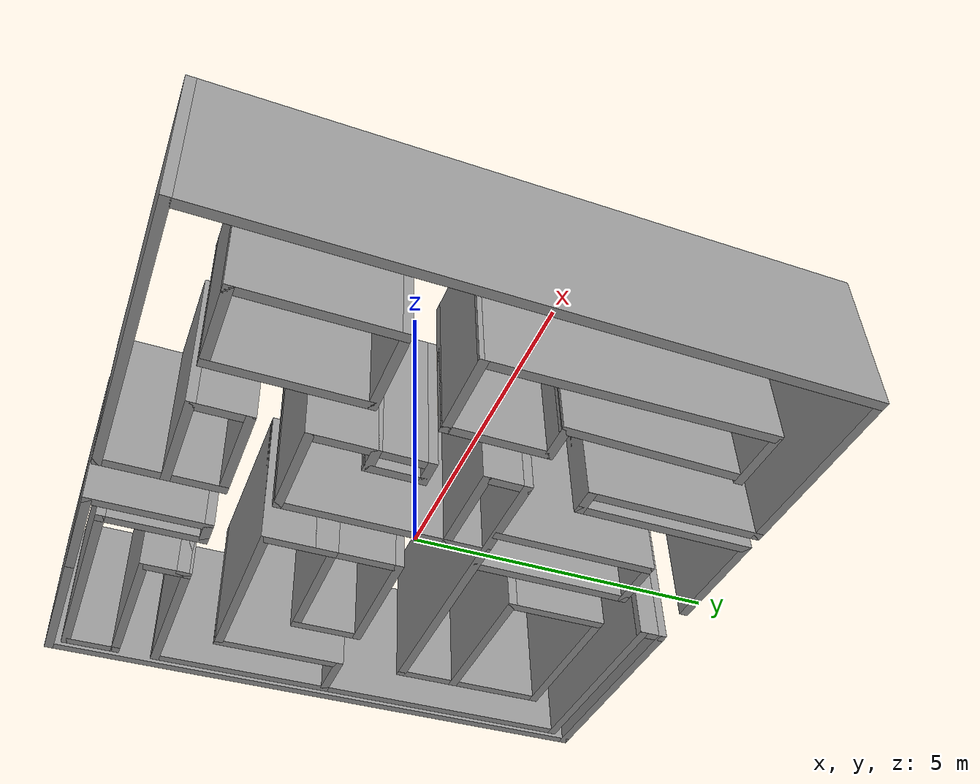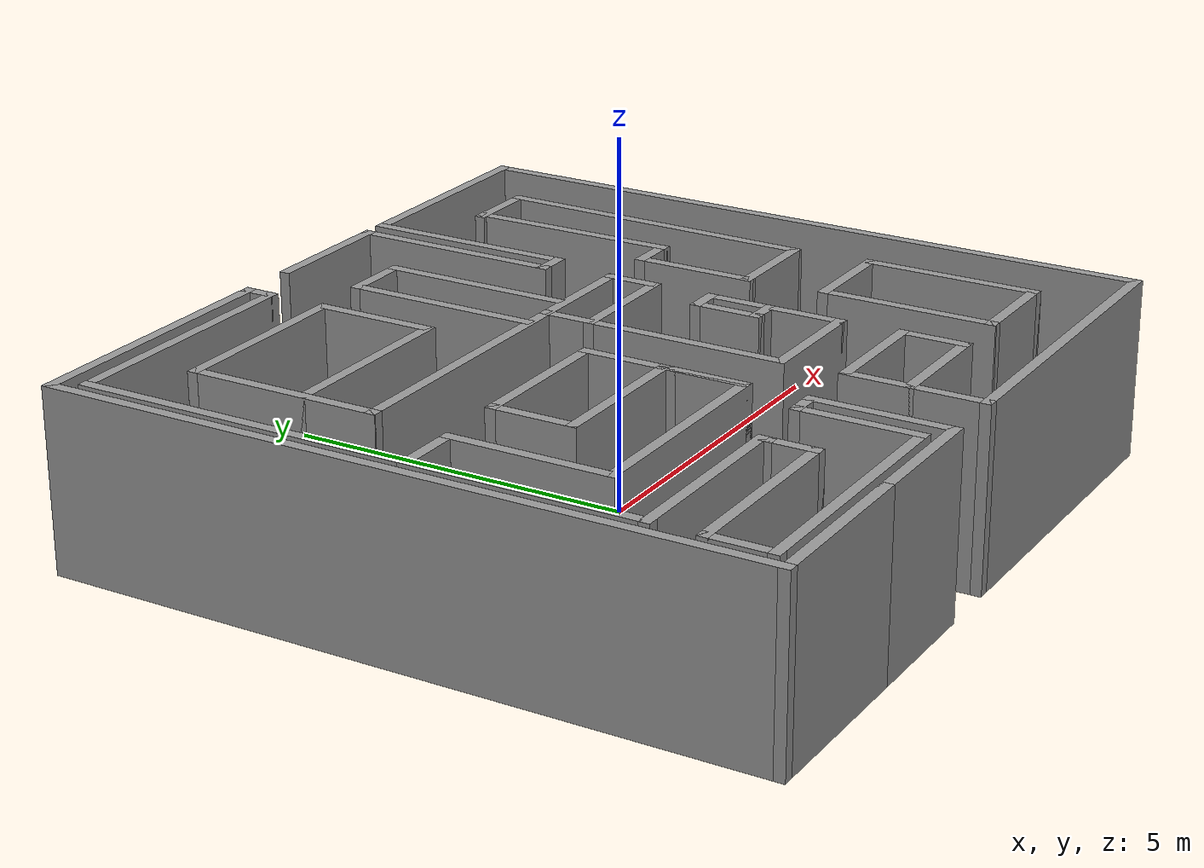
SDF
<?xml version='1.0'?>
<sdf version='1.6'>
  <model name='maze_final1'>
    <link name='Wall_10'>
      <pose frame=''>-2.95 -4.675 0 0 -0 3.14159</pose>
      <self_collide>0</self_collide>
      <enable_wind>0</enable_wind>
      <kinematic>0</kinematic>
      <visual name='Wall_10_Visual'>
        <pose frame=''>0 0 1.25 0 -0 0</pose>
        <geometry>
          <box>
            <size>3.75 0.15 2.5</size>
          </box>
        </geometry>
        <material>
          <script>
            <uri>file://media/materials/scripts/gazebo.material</uri>
            <name>Gazebo/Grey</name>
          </script>
          <ambient>1 1 1 1</ambient>
        </material>
        <meta>
          <layer>0</layer>
        </meta>
        <transparency>0</transparency>
        <cast_shadows>1</cast_shadows>
      </visual>
      <collision name='Wall_10_Collision'>
        <laser_retro>0</laser_retro>
        <max_contacts>10</max_contacts>
        <pose frame=''>0 0 1.25 0 -0 0</pose>
        <geometry>
          <box>
            <size>3.75 0.15 2.5</size>
          </box>
        </geometry>
        <surface>
          <friction>
            <ode>
              <mu>1</mu>
              <mu2>1</mu2>
              <fdir1>0 0 0</fdir1>
              <slip1>0</slip1>
              <slip2>0</slip2>
            </ode>
            <torsional>
              <coefficient>1</coefficient>
              <patch_radius>0</patch_radius>
              <surface_radius>0</surface_radius>
              <use_patch_radius>1</use_patch_radius>
              <ode>
                <slip>0</slip>
              </ode>
            </torsional>
          </friction>
          <bounce>
            <restitution_coefficient>0</restitution_coefficient>
            <threshold>1e+06</threshold>
          </bounce>
          <contact>
            <collide_without_contact>0</collide_without_contact>
            <collide_without_contact_bitmask>1</collide_without_contact_bitmask>
            <collide_bitmask>1</collide_bitmask>
            <ode>
              <soft_cfm>0</soft_cfm>
              <soft_erp>0.2</soft_erp>
              <kp>1e+13</kp>
              <kd>1</kd>
              <max_vel>0.01</max_vel>
              <min_depth>0</min_depth>
            </ode>
            <bullet>
              <split_impulse>1</split_impulse>
              <split_impulse_penetration_threshold>-0.01</split_impulse_penetration_threshold>
              <soft_cfm>0</soft_cfm>
              <soft_erp>0.2</soft_erp>
              <kp>1e+13</kp>
              <kd>1</kd>
            </bullet>
          </contact>
        </surface>
      </collision>
    </link>
    <link name='Wall_102'>
      <pose frame=''>-4.75 2.275 0 0 -0 1.5708</pose>
      <self_collide>0</self_collide>
      <enable_wind>0</enable_wind>
      <kinematic>0</kinematic>
      <visual name='Wall_102_Visual'>
        <pose frame=''>0 0 1.25 0 -0 0</pose>
        <geometry>
          <box>
            <size>4.75 0.15 2.5</size>
          </box>
        </geometry>
        <material>
          <script>
            <uri>file://media/materials/scripts/gazebo.material</uri>
            <name>Gazebo/Grey</name>
          </script>
          <ambient>1 1 1 1</ambient>
        </material>
        <meta>
          <layer>0</layer>
        </meta>
        <transparency>0</transparency>
        <cast_shadows>1</cast_shadows>
      </visual>
      <collision name='Wall_102_Collision'>
        <laser_retro>0</laser_retro>
        <max_contacts>10</max_contacts>
        <pose frame=''>0 0 1.25 0 -0 0</pose>
        <geometry>
          <box>
            <size>4.75 0.15 2.5</size>
          </box>
        </geometry>
        <surface>
          <friction>
            <ode>
              <mu>1</mu>
              <mu2>1</mu2>
              <fdir1>0 0 0</fdir1>
              <slip1>0</slip1>
              <slip2>0</slip2>
            </ode>
            <torsional>
              <coefficient>1</coefficient>
              <patch_radius>0</patch_radius>
              <surface_radius>0</surface_radius>
              <use_patch_radius>1</use_patch_radius>
              <ode>
                <slip>0</slip>
              </ode>
            </torsional>
          </friction>
          <bounce>
            <restitution_coefficient>0</restitution_coefficient>
            <threshold>1e+06</threshold>
          </bounce>
          <contact>
            <collide_without_contact>0</collide_without_contact>
            <collide_without_contact_bitmask>1</collide_without_contact_bitmask>
            <collide_bitmask>1</collide_bitmask>
            <ode>
              <soft_cfm>0</soft_cfm>
              <soft_erp>0.2</soft_erp>
              <kp>1e+13</kp>
              <kd>1</kd>
              <max_vel>0.01</max_vel>
              <min_depth>0</min_depth>
            </ode>
            <bullet>
              <split_impulse>1</split_impulse>
              <split_impulse_penetration_threshold>-0.01</split_impulse_penetration_threshold>
              <soft_cfm>0</soft_cfm>
              <soft_erp>0.2</soft_erp>
              <kp>1e+13</kp>
              <kd>1</kd>
            </bullet>
          </contact>
        </surface>
      </collision>
    </link>
    <link name='Wall_103'>
      <pose frame=''>-2.95 4.575 0 0 -0 0</pose>
      <self_collide>0</self_collide>
      <enable_wind>0</enable_wind>
      <kinematic>0</kinematic>
      <visual name='Wall_103_Visual'>
        <pose frame=''>0 0 1.25 0 -0 0</pose>
        <geometry>
          <box>
            <size>3.75 0.15 2.5</size>
          </box>
        </geometry>
        <material>
          <script>
            <uri>file://media/materials/scripts/gazebo.material</uri>
            <name>Gazebo/Grey</name>
          </script>
          <ambient>1 1 1 1</ambient>
        </material>
        <meta>
          <layer>0</layer>
        </meta>
        <transparency>0</transparency>
        <cast_shadows>1</cast_shadows>
      </visual>
      <collision name='Wall_103_Collision'>
        <laser_retro>0</laser_retro>
        <max_contacts>10</max_contacts>
        <pose frame=''>0 0 1.25 0 -0 0</pose>
        <geometry>
          <box>
            <size>3.75 0.15 2.5</size>
          </box>
        </geometry>
        <surface>
          <friction>
            <ode>
              <mu>1</mu>
              <mu2>1</mu2>
              <fdir1>0 0 0</fdir1>
              <slip1>0</slip1>
              <slip2>0</slip2>
            </ode>
            <torsional>
              <coefficient>1</coefficient>
              <patch_radius>0</patch_radius>
              <surface_radius>0</surface_radius>
              <use_patch_radius>1</use_patch_radius>
              <ode>
                <slip>0</slip>
              </ode>
            </torsional>
          </friction>
          <bounce>
            <restitution_coefficient>0</restitution_coefficient>
            <threshold>1e+06</threshold>
          </bounce>
          <contact>
            <collide_without_contact>0</collide_without_contact>
            <collide_without_contact_bitmask>1</collide_without_contact_bitmask>
            <collide_bitmask>1</collide_bitmask>
            <ode>
              <soft_cfm>0</soft_cfm>
              <soft_erp>0.2</soft_erp>
              <kp>1e+13</kp>
              <kd>1</kd>
              <max_vel>0.01</max_vel>
              <min_depth>0</min_depth>
            </ode>
            <bullet>
              <split_impulse>1</split_impulse>
              <split_impulse_penetration_threshold>-0.01</split_impulse_penetration_threshold>
              <soft_cfm>0</soft_cfm>
              <soft_erp>0.2</soft_erp>
              <kp>1e+13</kp>
              <kd>1</kd>
            </bullet>
          </contact>
        </surface>
      </collision>
    </link>
    <link name='Wall_104'>
      <pose frame=''>-1.15 4.75 0 0 -0 1.5708</pose>
      <self_collide>0</self_collide>
      <enable_wind>0</enable_wind>
      <kinematic>0</kinematic>
      <visual name='Wall_104_Visual'>
        <pose frame=''>0 0 1.25 0 -0 0</pose>
        <geometry>
          <box>
            <size>0.5 0.15 2.5</size>
          </box>
        </geometry>
        <material>
          <script>
            <uri>file://media/materials/scripts/gazebo.material</uri>
            <name>Gazebo/Grey</name>
          </script>
          <ambient>1 1 1 1</ambient>
        </material>
        <meta>
          <layer>0</layer>
        </meta>
        <transparency>0</transparency>
        <cast_shadows>1</cast_shadows>
      </visual>
      <collision name='Wall_104_Collision'>
        <laser_retro>0</laser_retro>
        <max_contacts>10</max_contacts>
        <pose frame=''>0 0 1.25 0 -0 0</pose>
        <geometry>
          <box>
            <size>0.5 0.15 2.5</size>
          </box>
        </geometry>
        <surface>
          <friction>
            <ode>
              <mu>1</mu>
              <mu2>1</mu2>
              <fdir1>0 0 0</fdir1>
              <slip1>0</slip1>
              <slip2>0</slip2>
            </ode>
            <torsional>
              <coefficient>1</coefficient>
              <patch_radius>0</patch_radius>
              <surface_radius>0</surface_radius>
              <use_patch_radius>1</use_patch_radius>
              <ode>
                <slip>0</slip>
              </ode>
            </torsional>
          </friction>
          <bounce>
            <restitution_coefficient>0</restitution_coefficient>
            <threshold>1e+06</threshold>
          </bounce>
          <contact>
            <collide_without_contact>0</collide_without_contact>
            <collide_without_contact_bitmask>1</collide_without_contact_bitmask>
            <collide_bitmask>1</collide_bitmask>
            <ode>
              <soft_cfm>0</soft_cfm>
              <soft_erp>0.2</soft_erp>
              <kp>1e+13</kp>
              <kd>1</kd>
              <max_vel>0.01</max_vel>
              <min_depth>0</min_depth>
            </ode>
            <bullet>
              <split_impulse>1</split_impulse>
              <split_impulse_penetration_threshold>-0.01</split_impulse_penetration_threshold>
              <soft_cfm>0</soft_cfm>
              <soft_erp>0.2</soft_erp>
              <kp>1e+13</kp>
              <kd>1</kd>
            </bullet>
          </contact>
        </surface>
      </collision>
    </link>
    <link name='Wall_107'>
      <pose frame=''>-2.45 3.725 0 0 -0 3.14159</pose>
      <self_collide>0</self_collide>
      <enable_wind>0</enable_wind>
      <kinematic>0</kinematic>
      <visual name='Wall_107_Visual'>
        <pose frame=''>0 0 1.25 0 -0 0</pose>
        <geometry>
          <box>
            <size>2.75 0.15 2.5</size>
          </box>
        </geometry>
        <material>
          <script>
            <uri>file://media/materials/scripts/gazebo.material</uri>
            <name>Gazebo/Grey</name>
          </script>
          <ambient>1 1 1 1</ambient>
        </material>
        <meta>
          <layer>0</layer>
        </meta>
        <transparency>0</transparency>
        <cast_shadows>1</cast_shadows>
      </visual>
      <collision name='Wall_107_Collision'>
        <laser_retro>0</laser_retro>
        <max_contacts>10</max_contacts>
        <pose frame=''>0 0 1.25 0 -0 0</pose>
        <geometry>
          <box>
            <size>2.75 0.15 2.5</size>
          </box>
        </geometry>
        <surface>
          <friction>
            <ode>
              <mu>1</mu>
              <mu2>1</mu2>
              <fdir1>0 0 0</fdir1>
              <slip1>0</slip1>
              <slip2>0</slip2>
            </ode>
            <torsional>
              <coefficient>1</coefficient>
              <patch_radius>0</patch_radius>
              <surface_radius>0</surface_radius>
              <use_patch_radius>1</use_patch_radius>
              <ode>
                <slip>0</slip>
              </ode>
            </torsional>
          </friction>
          <bounce>
            <restitution_coefficient>0</restitution_coefficient>
            <threshold>1e+06</threshold>
          </bounce>
          <contact>
            <collide_without_contact>0</collide_without_contact>
            <collide_without_contact_bitmask>1</collide_without_contact_bitmask>
            <collide_bitmask>1</collide_bitmask>
            <ode>
              <soft_cfm>0</soft_cfm>
              <soft_erp>0.2</soft_erp>
              <kp>1e+13</kp>
              <kd>1</kd>
              <max_vel>0.01</max_vel>
              <min_depth>0</min_depth>
            </ode>
            <bullet>
              <split_impulse>1</split_impulse>
              <split_impulse_penetration_threshold>-0.01</split_impulse_penetration_threshold>
              <soft_cfm>0</soft_cfm>
              <soft_erp>0.2</soft_erp>
              <kp>1e+13</kp>
              <kd>1</kd>
            </bullet>
          </contact>
        </surface>
      </collision>
    </link>
    <link name='Wall_108'>
      <pose frame=''>-3.75 2.425 0 0 0 -1.5708</pose>
      <self_collide>0</self_collide>
      <enable_wind>0</enable_wind>
      <kinematic>0</kinematic>
      <visual name='Wall_108_Visual'>
        <pose frame=''>0 0 1.25 0 -0 0</pose>
        <geometry>
          <box>
            <size>2.75 0.15 2.5</size>
          </box>
        </geometry>
        <material>
          <script>
            <uri>file://media/materials/scripts/gazebo.material</uri>
            <name>Gazebo/Grey</name>
          </script>
          <ambient>1 1 1 1</ambient>
        </material>
        <meta>
          <layer>0</layer>
        </meta>
        <transparency>0</transparency>
        <cast_shadows>1</cast_shadows>
      </visual>
      <collision name='Wall_108_Collision'>
        <laser_retro>0</laser_retro>
        <max_contacts>10</max_contacts>
        <pose frame=''>0 0 1.25 0 -0 0</pose>
        <geometry>
          <box>
            <size>2.75 0.15 2.5</size>
          </box>
        </geometry>
        <surface>
          <friction>
            <ode>
              <mu>1</mu>
              <mu2>1</mu2>
              <fdir1>0 0 0</fdir1>
              <slip1>0</slip1>
              <slip2>0</slip2>
            </ode>
            <torsional>
              <coefficient>1</coefficient>
              <patch_radius>0</patch_radius>
              <surface_radius>0</surface_radius>
              <use_patch_radius>1</use_patch_radius>
              <ode>
                <slip>0</slip>
              </ode>
            </torsional>
          </friction>
          <bounce>
            <restitution_coefficient>0</restitution_coefficient>
            <threshold>1e+06</threshold>
          </bounce>
          <contact>
            <collide_without_contact>0</collide_without_contact>
            <collide_without_contact_bitmask>1</collide_without_contact_bitmask>
            <collide_bitmask>1</collide_bitmask>
            <ode>
              <soft_cfm>0</soft_cfm>
              <soft_erp>0.2</soft_erp>
              <kp>1e+13</kp>
              <kd>1</kd>
              <max_vel>0.01</max_vel>
              <min_depth>0</min_depth>
            </ode>
            <bullet>
              <split_impulse>1</split_impulse>
              <split_impulse_penetration_threshold>-0.01</split_impulse_penetration_threshold>
              <soft_cfm>0</soft_cfm>
              <soft_erp>0.2</soft_erp>
              <kp>1e+13</kp>
              <kd>1</kd>
            </bullet>
          </contact>
        </surface>
      </collision>
    </link>
    <link name='Wall_109'>
      <pose frame=''>-1.825 1.125 0 0 -0 0</pose>
      <self_collide>0</self_collide>
      <enable_wind>0</enable_wind>
      <kinematic>0</kinematic>
      <visual name='Wall_109_Visual'>
        <pose frame=''>0 0 1.25 0 -0 0</pose>
        <geometry>
          <box>
            <size>4 0.15 2.5</size>
          </box>
        </geometry>
        <material>
          <script>
            <uri>file://media/materials/scripts/gazebo.material</uri>
            <name>Gazebo/Grey</name>
          </script>
          <ambient>1 1 1 1</ambient>
        </material>
        <meta>
          <layer>0</layer>
        </meta>
        <transparency>0</transparency>
        <cast_shadows>1</cast_shadows>
      </visual>
      <collision name='Wall_109_Collision'>
        <laser_retro>0</laser_retro>
        <max_contacts>10</max_contacts>
        <pose frame=''>0 0 1.25 0 -0 0</pose>
        <geometry>
          <box>
            <size>4 0.15 2.5</size>
          </box>
        </geometry>
        <surface>
          <friction>
            <ode>
              <mu>1</mu>
              <mu2>1</mu2>
              <fdir1>0 0 0</fdir1>
              <slip1>0</slip1>
              <slip2>0</slip2>
            </ode>
            <torsional>
              <coefficient>1</coefficient>
              <patch_radius>0</patch_radius>
              <surface_radius>0</surface_radius>
              <use_patch_radius>1</use_patch_radius>
              <ode>
                <slip>0</slip>
              </ode>
            </torsional>
          </friction>
          <bounce>
            <restitution_coefficient>0</restitution_coefficient>
            <threshold>1e+06</threshold>
          </bounce>
          <contact>
            <collide_without_contact>0</collide_without_contact>
            <collide_without_contact_bitmask>1</collide_without_contact_bitmask>
            <collide_bitmask>1</collide_bitmask>
            <ode>
              <soft_cfm>0</soft_cfm>
              <soft_erp>0.2</soft_erp>
              <kp>1e+13</kp>
              <kd>1</kd>
              <max_vel>0.01</max_vel>
              <min_depth>0</min_depth>
            </ode>
            <bullet>
              <split_impulse>1</split_impulse>
              <split_impulse_penetration_threshold>-0.01</split_impulse_penetration_threshold>
              <soft_cfm>0</soft_cfm>
              <soft_erp>0.2</soft_erp>
              <kp>1e+13</kp>
              <kd>1</kd>
            </bullet>
          </contact>
        </surface>
      </collision>
    </link>
    <link name='Wall_11'>
      <pose frame=''>-4.75 -4.25 0 0 -0 1.5708</pose>
      <self_collide>0</self_collide>
      <enable_wind>0</enable_wind>
      <kinematic>0</kinematic>
      <visual name='Wall_11_Visual'>
        <pose frame=''>0 0 1.25 0 -0 0</pose>
        <geometry>
          <box>
            <size>1 0.15 2.5</size>
          </box>
        </geometry>
        <material>
          <script>
            <uri>file://media/materials/scripts/gazebo.material</uri>
            <name>Gazebo/Grey</name>
          </script>
          <ambient>1 1 1 1</ambient>
        </material>
        <meta>
          <layer>0</layer>
        </meta>
        <transparency>0</transparency>
        <cast_shadows>1</cast_shadows>
      </visual>
      <collision name='Wall_11_Collision'>
        <laser_retro>0</laser_retro>
        <max_contacts>10</max_contacts>
        <pose frame=''>0 0 1.25 0 -0 0</pose>
        <geometry>
          <box>
            <size>1 0.15 2.5</size>
          </box>
        </geometry>
        <surface>
          <friction>
            <ode>
              <mu>1</mu>
              <mu2>1</mu2>
              <fdir1>0 0 0</fdir1>
              <slip1>0</slip1>
              <slip2>0</slip2>
            </ode>
            <torsional>
              <coefficient>1</coefficient>
              <patch_radius>0</patch_radius>
              <surface_radius>0</surface_radius>
              <use_patch_radius>1</use_patch_radius>
              <ode>
                <slip>0</slip>
              </ode>
            </torsional>
          </friction>
          <bounce>
            <restitution_coefficient>0</restitution_coefficient>
            <threshold>1e+06</threshold>
          </bounce>
          <contact>
            <collide_without_contact>0</collide_without_contact>
            <collide_without_contact_bitmask>1</collide_without_contact_bitmask>
            <collide_bitmask>1</collide_bitmask>
            <ode>
              <soft_cfm>0</soft_cfm>
              <soft_erp>0.2</soft_erp>
              <kp>1e+13</kp>
              <kd>1</kd>
              <max_vel>0.01</max_vel>
              <min_depth>0</min_depth>
            </ode>
            <bullet>
              <split_impulse>1</split_impulse>
              <split_impulse_penetration_threshold>-0.01</split_impulse_penetration_threshold>
              <soft_cfm>0</soft_cfm>
              <soft_erp>0.2</soft_erp>
              <kp>1e+13</kp>
              <kd>1</kd>
            </bullet>
          </contact>
        </surface>
      </collision>
    </link>
    <link name='Wall_112'>
      <pose frame=''>0.1 -0.55 0 0 0 -1.5708</pose>
      <self_collide>0</self_collide>
      <enable_wind>0</enable_wind>
      <kinematic>0</kinematic>
      <visual name='Wall_112_Visual'>
        <pose frame=''>0 0 1.25 0 -0 0</pose>
        <geometry>
          <box>
            <size>3.5 0.15 2.5</size>
          </box>
        </geometry>
        <material>
          <script>
            <uri>file://media/materials/scripts/gazebo.material</uri>
            <name>Gazebo/Grey</name>
          </script>
          <ambient>1 1 1 1</ambient>
        </material>
        <meta>
          <layer>0</layer>
        </meta>
        <transparency>0</transparency>
        <cast_shadows>1</cast_shadows>
      </visual>
      <collision name='Wall_112_Collision'>
        <laser_retro>0</laser_retro>
        <max_contacts>10</max_contacts>
        <pose frame=''>0 0 1.25 0 -0 0</pose>
        <geometry>
          <box>
            <size>3.5 0.15 2.5</size>
          </box>
        </geometry>
        <surface>
          <friction>
            <ode>
              <mu>1</mu>
              <mu2>1</mu2>
              <fdir1>0 0 0</fdir1>
              <slip1>0</slip1>
              <slip2>0</slip2>
            </ode>
            <torsional>
              <coefficient>1</coefficient>
              <patch_radius>0</patch_radius>
              <surface_radius>0</surface_radius>
              <use_patch_radius>1</use_patch_radius>
              <ode>
                <slip>0</slip>
              </ode>
            </torsional>
          </friction>
          <bounce>
            <restitution_coefficient>0</restitution_coefficient>
            <threshold>1e+06</threshold>
          </bounce>
          <contact>
            <collide_without_contact>0</collide_without_contact>
            <collide_without_contact_bitmask>1</collide_without_contact_bitmask>
            <collide_bitmask>1</collide_bitmask>
            <ode>
              <soft_cfm>0</soft_cfm>
              <soft_erp>0.2</soft_erp>
              <kp>1e+13</kp>
              <kd>1</kd>
              <max_vel>0.01</max_vel>
              <min_depth>0</min_depth>
            </ode>
            <bullet>
              <split_impulse>1</split_impulse>
              <split_impulse_penetration_threshold>-0.01</split_impulse_penetration_threshold>
              <soft_cfm>0</soft_cfm>
              <soft_erp>0.2</soft_erp>
              <kp>1e+13</kp>
              <kd>1</kd>
            </bullet>
          </contact>
        </surface>
      </collision>
    </link>
    <link name='Wall_113'>
      <pose frame=''>0.9 -2.225 0 0 -0 0</pose>
      <self_collide>0</self_collide>
      <enable_wind>0</enable_wind>
      <kinematic>0</kinematic>
      <visual name='Wall_113_Visual'>
        <pose frame=''>0 0 1.25 0 -0 0</pose>
        <geometry>
          <box>
            <size>1.75 0.15 2.5</size>
          </box>
        </geometry>
        <material>
          <script>
            <uri>file://media/materials/scripts/gazebo.material</uri>
            <name>Gazebo/Grey</name>
          </script>
          <ambient>1 1 1 1</ambient>
        </material>
        <meta>
          <layer>0</layer>
        </meta>
        <transparency>0</transparency>
        <cast_shadows>1</cast_shadows>
      </visual>
      <collision name='Wall_113_Collision'>
        <laser_retro>0</laser_retro>
        <max_contacts>10</max_contacts>
        <pose frame=''>0 0 1.25 0 -0 0</pose>
        <geometry>
          <box>
            <size>1.75 0.15 2.5</size>
          </box>
        </geometry>
        <surface>
          <friction>
            <ode>
              <mu>1</mu>
              <mu2>1</mu2>
              <fdir1>0 0 0</fdir1>
              <slip1>0</slip1>
              <slip2>0</slip2>
            </ode>
            <torsional>
              <coefficient>1</coefficient>
              <patch_radius>0</patch_radius>
              <surface_radius>0</surface_radius>
              <use_patch_radius>1</use_patch_radius>
              <ode>
                <slip>0</slip>
              </ode>
            </torsional>
          </friction>
          <bounce>
            <restitution_coefficient>0</restitution_coefficient>
            <threshold>1e+06</threshold>
          </bounce>
          <contact>
            <collide_without_contact>0</collide_without_contact>
            <collide_without_contact_bitmask>1</collide_without_contact_bitmask>
            <collide_bitmask>1</collide_bitmask>
            <ode>
              <soft_cfm>0</soft_cfm>
              <soft_erp>0.2</soft_erp>
              <kp>1e+13</kp>
              <kd>1</kd>
              <max_vel>0.01</max_vel>
              <min_depth>0</min_depth>
            </ode>
            <bullet>
              <split_impulse>1</split_impulse>
              <split_impulse_penetration_threshold>-0.01</split_impulse_penetration_threshold>
              <soft_cfm>0</soft_cfm>
              <soft_erp>0.2</soft_erp>
              <kp>1e+13</kp>
              <kd>1</kd>
            </bullet>
          </contact>
        </surface>
      </collision>
    </link>
    <link name='Wall_114'>
      <pose frame=''>1.7 -1.3 0 0 -0 1.5708</pose>
      <self_collide>0</self_collide>
      <enable_wind>0</enable_wind>
      <kinematic>0</kinematic>
      <visual name='Wall_114_Visual'>
        <pose frame=''>0 0 1.25 0 -0 0</pose>
        <geometry>
          <box>
            <size>2 0.15 2.5</size>
          </box>
        </geometry>
        <material>
          <script>
            <uri>file://media/materials/scripts/gazebo.material</uri>
            <name>Gazebo/Grey</name>
          </script>
          <ambient>1 1 1 1</ambient>
        </material>
        <meta>
          <layer>0</layer>
        </meta>
        <transparency>0</transparency>
        <cast_shadows>1</cast_shadows>
      </visual>
      <collision name='Wall_114_Collision'>
        <laser_retro>0</laser_retro>
        <max_contacts>10</max_contacts>
        <pose frame=''>0 0 1.25 0 -0 0</pose>
        <geometry>
          <box>
            <size>2 0.15 2.5</size>
          </box>
        </geometry>
        <surface>
          <friction>
            <ode>
              <mu>1</mu>
              <mu2>1</mu2>
              <fdir1>0 0 0</fdir1>
              <slip1>0</slip1>
              <slip2>0</slip2>
            </ode>
            <torsional>
              <coefficient>1</coefficient>
              <patch_radius>0</patch_radius>
              <surface_radius>0</surface_radius>
              <use_patch_radius>1</use_patch_radius>
              <ode>
                <slip>0</slip>
              </ode>
            </torsional>
          </friction>
          <bounce>
            <restitution_coefficient>0</restitution_coefficient>
            <threshold>1e+06</threshold>
          </bounce>
          <contact>
            <collide_without_contact>0</collide_without_contact>
            <collide_without_contact_bitmask>1</collide_without_contact_bitmask>
            <collide_bitmask>1</collide_bitmask>
            <ode>
              <soft_cfm>0</soft_cfm>
              <soft_erp>0.2</soft_erp>
              <kp>1e+13</kp>
              <kd>1</kd>
              <max_vel>0.01</max_vel>
              <min_depth>0</min_depth>
            </ode>
            <bullet>
              <split_impulse>1</split_impulse>
              <split_impulse_penetration_threshold>-0.01</split_impulse_penetration_threshold>
              <soft_cfm>0</soft_cfm>
              <soft_erp>0.2</soft_erp>
              <kp>1e+13</kp>
              <kd>1</kd>
            </bullet>
          </contact>
        </surface>
      </collision>
    </link>
    <link name='Wall_115'>
      <pose frame=''>1.525 -0.375 0 0 -0 3.14159</pose>
      <self_collide>0</self_collide>
      <enable_wind>0</enable_wind>
      <kinematic>0</kinematic>
      <visual name='Wall_115_Visual'>
        <pose frame=''>0 0 1.25 0 -0 0</pose>
        <geometry>
          <box>
            <size>0.5 0.15 2.5</size>
          </box>
        </geometry>
        <material>
          <script>
            <uri>file://media/materials/scripts/gazebo.material</uri>
            <name>Gazebo/Grey</name>
          </script>
          <ambient>1 1 1 1</ambient>
        </material>
        <meta>
          <layer>0</layer>
        </meta>
        <transparency>0</transparency>
        <cast_shadows>1</cast_shadows>
      </visual>
      <collision name='Wall_115_Collision'>
        <laser_retro>0</laser_retro>
        <max_contacts>10</max_contacts>
        <pose frame=''>0 0 1.25 0 -0 0</pose>
        <geometry>
          <box>
            <size>0.5 0.15 2.5</size>
          </box>
        </geometry>
        <surface>
          <friction>
            <ode>
              <mu>1</mu>
              <mu2>1</mu2>
              <fdir1>0 0 0</fdir1>
              <slip1>0</slip1>
              <slip2>0</slip2>
            </ode>
            <torsional>
              <coefficient>1</coefficient>
              <patch_radius>0</patch_radius>
              <surface_radius>0</surface_radius>
              <use_patch_radius>1</use_patch_radius>
              <ode>
                <slip>0</slip>
              </ode>
            </torsional>
          </friction>
          <bounce>
            <restitution_coefficient>0</restitution_coefficient>
            <threshold>1e+06</threshold>
          </bounce>
          <contact>
            <collide_without_contact>0</collide_without_contact>
            <collide_without_contact_bitmask>1</collide_without_contact_bitmask>
            <collide_bitmask>1</collide_bitmask>
            <ode>
              <soft_cfm>0</soft_cfm>
              <soft_erp>0.2</soft_erp>
              <kp>1e+13</kp>
              <kd>1</kd>
              <max_vel>0.01</max_vel>
              <min_depth>0</min_depth>
            </ode>
            <bullet>
              <split_impulse>1</split_impulse>
              <split_impulse_penetration_threshold>-0.01</split_impulse_penetration_threshold>
              <soft_cfm>0</soft_cfm>
              <soft_erp>0.2</soft_erp>
              <kp>1e+13</kp>
              <kd>1</kd>
            </bullet>
          </contact>
        </surface>
      </collision>
    </link>
    <link name='Wall_116'>
      <pose frame=''>1.35 -0.8 0 0 0 -1.5708</pose>
      <self_collide>0</self_collide>
      <enable_wind>0</enable_wind>
      <kinematic>0</kinematic>
      <visual name='Wall_116_Visual'>
        <pose frame=''>0 0 1.25 0 -0 0</pose>
        <geometry>
          <box>
            <size>1 0.15 2.5</size>
          </box>
        </geometry>
        <material>
          <script>
            <uri>file://media/materials/scripts/gazebo.material</uri>
            <name>Gazebo/Grey</name>
          </script>
          <ambient>1 1 1 1</ambient>
        </material>
        <meta>
          <layer>0</layer>
        </meta>
        <transparency>0</transparency>
        <cast_shadows>1</cast_shadows>
      </visual>
      <collision name='Wall_116_Collision'>
        <laser_retro>0</laser_retro>
        <max_contacts>10</max_contacts>
        <pose frame=''>0 0 1.25 0 -0 0</pose>
        <geometry>
          <box>
            <size>1 0.15 2.5</size>
          </box>
        </geometry>
        <surface>
          <friction>
            <ode>
              <mu>1</mu>
              <mu2>1</mu2>
              <fdir1>0 0 0</fdir1>
              <slip1>0</slip1>
              <slip2>0</slip2>
            </ode>
            <torsional>
              <coefficient>1</coefficient>
              <patch_radius>0</patch_radius>
              <surface_radius>0</surface_radius>
              <use_patch_radius>1</use_patch_radius>
              <ode>
                <slip>0</slip>
              </ode>
            </torsional>
          </friction>
          <bounce>
            <restitution_coefficient>0</restitution_coefficient>
            <threshold>1e+06</threshold>
          </bounce>
          <contact>
            <collide_without_contact>0</collide_without_contact>
            <collide_without_contact_bitmask>1</collide_without_contact_bitmask>
            <collide_bitmask>1</collide_bitmask>
            <ode>
              <soft_cfm>0</soft_cfm>
              <soft_erp>0.2</soft_erp>
              <kp>1e+13</kp>
              <kd>1</kd>
              <max_vel>0.01</max_vel>
              <min_depth>0</min_depth>
            </ode>
            <bullet>
              <split_impulse>1</split_impulse>
              <split_impulse_penetration_threshold>-0.01</split_impulse_penetration_threshold>
              <soft_cfm>0</soft_cfm>
              <soft_erp>0.2</soft_erp>
              <kp>1e+13</kp>
              <kd>1</kd>
            </bullet>
          </contact>
        </surface>
      </collision>
    </link>
    <link name='Wall_117'>
      <pose frame=''>1.525 -1.225 0 0 -0 0</pose>
      <self_collide>0</self_collide>
      <enable_wind>0</enable_wind>
      <kinematic>0</kinematic>
      <visual name='Wall_117_Visual'>
        <pose frame=''>0 0 1.25 0 -0 0</pose>
        <geometry>
          <box>
            <size>0.5 0.15 2.5</size>
          </box>
        </geometry>
        <material>
          <script>
            <uri>file://media/materials/scripts/gazebo.material</uri>
            <name>Gazebo/Grey</name>
          </script>
          <ambient>1 1 1 1</ambient>
        </material>
        <meta>
          <layer>0</layer>
        </meta>
        <transparency>0</transparency>
        <cast_shadows>1</cast_shadows>
      </visual>
      <collision name='Wall_117_Collision'>
        <laser_retro>0</laser_retro>
        <max_contacts>10</max_contacts>
        <pose frame=''>0 0 1.25 0 -0 0</pose>
        <geometry>
          <box>
            <size>0.5 0.15 2.5</size>
          </box>
        </geometry>
        <surface>
          <friction>
            <ode>
              <mu>1</mu>
              <mu2>1</mu2>
              <fdir1>0 0 0</fdir1>
              <slip1>0</slip1>
              <slip2>0</slip2>
            </ode>
            <torsional>
              <coefficient>1</coefficient>
              <patch_radius>0</patch_radius>
              <surface_radius>0</surface_radius>
              <use_patch_radius>1</use_patch_radius>
              <ode>
                <slip>0</slip>
              </ode>
            </torsional>
          </friction>
          <bounce>
            <restitution_coefficient>0</restitution_coefficient>
            <threshold>1e+06</threshold>
          </bounce>
          <contact>
            <collide_without_contact>0</collide_without_contact>
            <collide_without_contact_bitmask>1</collide_without_contact_bitmask>
            <collide_bitmask>1</collide_bitmask>
            <ode>
              <soft_cfm>0</soft_cfm>
              <soft_erp>0.2</soft_erp>
              <kp>1e+13</kp>
              <kd>1</kd>
              <max_vel>0.01</max_vel>
              <min_depth>0</min_depth>
            </ode>
            <bullet>
              <split_impulse>1</split_impulse>
              <split_impulse_penetration_threshold>-0.01</split_impulse_penetration_threshold>
              <soft_cfm>0</soft_cfm>
              <soft_erp>0.2</soft_erp>
              <kp>1e+13</kp>
              <kd>1</kd>
            </bullet>
          </contact>
        </surface>
      </collision>
    </link>
    <link name='Wall_12'>
      <pose frame=''>-3.45 -3.825 0 0 -0 0</pose>
      <self_collide>0</self_collide>
      <enable_wind>0</enable_wind>
      <kinematic>0</kinematic>
      <visual name='Wall_12_Visual'>
        <pose frame=''>0 0 1.25 0 -0 0</pose>
        <geometry>
          <box>
            <size>2.75 0.15 2.5</size>
          </box>
        </geometry>
        <material>
          <script>
            <uri>file://media/materials/scripts/gazebo.material</uri>
            <name>Gazebo/Grey</name>
          </script>
          <ambient>1 1 1 1</ambient>
        </material>
        <meta>
          <layer>0</layer>
        </meta>
        <transparency>0</transparency>
        <cast_shadows>1</cast_shadows>
      </visual>
      <collision name='Wall_12_Collision'>
        <laser_retro>0</laser_retro>
        <max_contacts>10</max_contacts>
        <pose frame=''>0 0 1.25 0 -0 0</pose>
        <geometry>
          <box>
            <size>2.75 0.15 2.5</size>
          </box>
        </geometry>
        <surface>
          <friction>
            <ode>
              <mu>1</mu>
              <mu2>1</mu2>
              <fdir1>0 0 0</fdir1>
              <slip1>0</slip1>
              <slip2>0</slip2>
            </ode>
            <torsional>
              <coefficient>1</coefficient>
              <patch_radius>0</patch_radius>
              <surface_radius>0</surface_radius>
              <use_patch_radius>1</use_patch_radius>
              <ode>
                <slip>0</slip>
              </ode>
            </torsional>
          </friction>
          <bounce>
            <restitution_coefficient>0</restitution_coefficient>
            <threshold>1e+06</threshold>
          </bounce>
          <contact>
            <collide_without_contact>0</collide_without_contact>
            <collide_without_contact_bitmask>1</collide_without_contact_bitmask>
            <collide_bitmask>1</collide_bitmask>
            <ode>
              <soft_cfm>0</soft_cfm>
              <soft_erp>0.2</soft_erp>
              <kp>1e+13</kp>
              <kd>1</kd>
              <max_vel>0.01</max_vel>
              <min_depth>0</min_depth>
            </ode>
            <bullet>
              <split_impulse>1</split_impulse>
              <split_impulse_penetration_threshold>-0.01</split_impulse_penetration_threshold>
              <soft_cfm>0</soft_cfm>
              <soft_erp>0.2</soft_erp>
              <kp>1e+13</kp>
              <kd>1</kd>
            </bullet>
          </contact>
        </surface>
      </collision>
    </link>
    <link name='Wall_120'>
      <pose frame=''>0.9 0.475 0 0 -0 3.14159</pose>
      <self_collide>0</self_collide>
      <enable_wind>0</enable_wind>
      <kinematic>0</kinematic>
      <visual name='Wall_120_Visual'>
        <pose frame=''>0 0 1.25 0 -0 0</pose>
        <geometry>
          <box>
            <size>1.75 0.15 2.5</size>
          </box>
        </geometry>
        <material>
          <script>
            <uri>file://media/materials/scripts/gazebo.material</uri>
            <name>Gazebo/Grey</name>
          </script>
          <ambient>1 1 1 1</ambient>
        </material>
        <meta>
          <layer>0</layer>
        </meta>
        <transparency>0</transparency>
        <cast_shadows>1</cast_shadows>
      </visual>
      <collision name='Wall_120_Collision'>
        <laser_retro>0</laser_retro>
        <max_contacts>10</max_contacts>
        <pose frame=''>0 0 1.25 0 -0 0</pose>
        <geometry>
          <box>
            <size>1.75 0.15 2.5</size>
          </box>
        </geometry>
        <surface>
          <friction>
            <ode>
              <mu>1</mu>
              <mu2>1</mu2>
              <fdir1>0 0 0</fdir1>
              <slip1>0</slip1>
              <slip2>0</slip2>
            </ode>
            <torsional>
              <coefficient>1</coefficient>
              <patch_radius>0</patch_radius>
              <surface_radius>0</surface_radius>
              <use_patch_radius>1</use_patch_radius>
              <ode>
                <slip>0</slip>
              </ode>
            </torsional>
          </friction>
          <bounce>
            <restitution_coefficient>0</restitution_coefficient>
            <threshold>1e+06</threshold>
          </bounce>
          <contact>
            <collide_without_contact>0</collide_without_contact>
            <collide_without_contact_bitmask>1</collide_without_contact_bitmask>
            <collide_bitmask>1</collide_bitmask>
            <ode>
              <soft_cfm>0</soft_cfm>
              <soft_erp>0.2</soft_erp>
              <kp>1e+13</kp>
              <kd>1</kd>
              <max_vel>0.01</max_vel>
              <min_depth>0</min_depth>
            </ode>
            <bullet>
              <split_impulse>1</split_impulse>
              <split_impulse_penetration_threshold>-0.01</split_impulse_penetration_threshold>
              <soft_cfm>0</soft_cfm>
              <soft_erp>0.2</soft_erp>
              <kp>1e+13</kp>
              <kd>1</kd>
            </bullet>
          </contact>
        </surface>
      </collision>
    </link>
    <link name='Wall_122'>
      <pose frame=''>-1.15 2.925 0 0 0 -1.5708</pose>
      <self_collide>0</self_collide>
      <enable_wind>0</enable_wind>
      <kinematic>0</kinematic>
      <visual name='Wall_122_Visual'>
        <pose frame=''>0 0 1.25 0 -0 0</pose>
        <geometry>
          <box>
            <size>1.75 0.15 2.5</size>
          </box>
        </geometry>
        <material>
          <script>
            <uri>file://media/materials/scripts/gazebo.material</uri>
            <name>Gazebo/Grey</name>
          </script>
          <ambient>1 1 1 1</ambient>
        </material>
        <meta>
          <layer>0</layer>
        </meta>
        <transparency>0</transparency>
        <cast_shadows>1</cast_shadows>
      </visual>
      <collision name='Wall_122_Collision'>
        <laser_retro>0</laser_retro>
        <max_contacts>10</max_contacts>
        <pose frame=''>0 0 1.25 0 -0 0</pose>
        <geometry>
          <box>
            <size>1.75 0.15 2.5</size>
          </box>
        </geometry>
        <surface>
          <friction>
            <ode>
              <mu>1</mu>
              <mu2>1</mu2>
              <fdir1>0 0 0</fdir1>
              <slip1>0</slip1>
              <slip2>0</slip2>
            </ode>
            <torsional>
              <coefficient>1</coefficient>
              <patch_radius>0</patch_radius>
              <surface_radius>0</surface_radius>
              <use_patch_radius>1</use_patch_radius>
              <ode>
                <slip>0</slip>
              </ode>
            </torsional>
          </friction>
          <bounce>
            <restitution_coefficient>0</restitution_coefficient>
            <threshold>1e+06</threshold>
          </bounce>
          <contact>
            <collide_without_contact>0</collide_without_contact>
            <collide_without_contact_bitmask>1</collide_without_contact_bitmask>
            <collide_bitmask>1</collide_bitmask>
            <ode>
              <soft_cfm>0</soft_cfm>
              <soft_erp>0.2</soft_erp>
              <kp>1e+13</kp>
              <kd>1</kd>
              <max_vel>0.01</max_vel>
              <min_depth>0</min_depth>
            </ode>
            <bullet>
              <split_impulse>1</split_impulse>
              <split_impulse_penetration_threshold>-0.01</split_impulse_penetration_threshold>
              <soft_cfm>0</soft_cfm>
              <soft_erp>0.2</soft_erp>
              <kp>1e+13</kp>
              <kd>1</kd>
            </bullet>
          </contact>
        </surface>
      </collision>
    </link>
    <link name='Wall_123'>
      <pose frame=''>-2.45 2.125 0 0 -0 3.14159</pose>
      <self_collide>0</self_collide>
      <enable_wind>0</enable_wind>
      <kinematic>0</kinematic>
      <visual name='Wall_123_Visual'>
        <pose frame=''>0 0 1.25 0 -0 0</pose>
        <geometry>
          <box>
            <size>2.75 0.15 2.5</size>
          </box>
        </geometry>
        <material>
          <script>
            <uri>file://media/materials/scripts/gazebo.material</uri>
            <name>Gazebo/Grey</name>
          </script>
          <ambient>1 1 1 1</ambient>
        </material>
        <meta>
          <layer>0</layer>
        </meta>
        <transparency>0</transparency>
        <cast_shadows>1</cast_shadows>
      </visual>
      <collision name='Wall_123_Collision'>
        <laser_retro>0</laser_retro>
        <max_contacts>10</max_contacts>
        <pose frame=''>0 0 1.25 0 -0 0</pose>
        <geometry>
          <box>
            <size>2.75 0.15 2.5</size>
          </box>
        </geometry>
        <surface>
          <friction>
            <ode>
              <mu>1</mu>
              <mu2>1</mu2>
              <fdir1>0 0 0</fdir1>
              <slip1>0</slip1>
              <slip2>0</slip2>
            </ode>
            <torsional>
              <coefficient>1</coefficient>
              <patch_radius>0</patch_radius>
              <surface_radius>0</surface_radius>
              <use_patch_radius>1</use_patch_radius>
              <ode>
                <slip>0</slip>
              </ode>
            </torsional>
          </friction>
          <bounce>
            <restitution_coefficient>0</restitution_coefficient>
            <threshold>1e+06</threshold>
          </bounce>
          <contact>
            <collide_without_contact>0</collide_without_contact>
            <collide_without_contact_bitmask>1</collide_without_contact_bitmask>
            <collide_bitmask>1</collide_bitmask>
            <ode>
              <soft_cfm>0</soft_cfm>
              <soft_erp>0.2</soft_erp>
              <kp>1e+13</kp>
              <kd>1</kd>
              <max_vel>0.01</max_vel>
              <min_depth>0</min_depth>
            </ode>
            <bullet>
              <split_impulse>1</split_impulse>
              <split_impulse_penetration_threshold>-0.01</split_impulse_penetration_threshold>
              <soft_cfm>0</soft_cfm>
              <soft_erp>0.2</soft_erp>
              <kp>1e+13</kp>
              <kd>1</kd>
            </bullet>
          </contact>
        </surface>
      </collision>
    </link>
    <link name='Wall_128'>
      <pose frame=''>0.625 4.925 0 0 -0 0</pose>
      <self_collide>0</self_collide>
      <enable_wind>0</enable_wind>
      <kinematic>0</kinematic>
      <visual name='Wall_128_Visual'>
        <pose frame=''>0 0 1.25 0 -0 0</pose>
        <geometry>
          <box>
            <size>2 0.15 2.5</size>
          </box>
        </geometry>
        <material>
          <script>
            <uri>file://media/materials/scripts/gazebo.material</uri>
            <name>Gazebo/Grey</name>
          </script>
          <ambient>1 1 1 1</ambient>
        </material>
        <meta>
          <layer>0</layer>
        </meta>
        <transparency>0</transparency>
        <cast_shadows>1</cast_shadows>
      </visual>
      <collision name='Wall_128_Collision'>
        <laser_retro>0</laser_retro>
        <max_contacts>10</max_contacts>
        <pose frame=''>0 0 1.25 0 -0 0</pose>
        <geometry>
          <box>
            <size>2 0.15 2.5</size>
          </box>
        </geometry>
        <surface>
          <friction>
            <ode>
              <mu>1</mu>
              <mu2>1</mu2>
              <fdir1>0 0 0</fdir1>
              <slip1>0</slip1>
              <slip2>0</slip2>
            </ode>
            <torsional>
              <coefficient>1</coefficient>
              <patch_radius>0</patch_radius>
              <surface_radius>0</surface_radius>
              <use_patch_radius>1</use_patch_radius>
              <ode>
                <slip>0</slip>
              </ode>
            </torsional>
          </friction>
          <bounce>
            <restitution_coefficient>0</restitution_coefficient>
            <threshold>1e+06</threshold>
          </bounce>
          <contact>
            <collide_without_contact>0</collide_without_contact>
            <collide_without_contact_bitmask>1</collide_without_contact_bitmask>
            <collide_bitmask>1</collide_bitmask>
            <ode>
              <soft_cfm>0</soft_cfm>
              <soft_erp>0.2</soft_erp>
              <kp>1e+13</kp>
              <kd>1</kd>
              <max_vel>0.01</max_vel>
              <min_depth>0</min_depth>
            </ode>
            <bullet>
              <split_impulse>1</split_impulse>
              <split_impulse_penetration_threshold>-0.01</split_impulse_penetration_threshold>
              <soft_cfm>0</soft_cfm>
              <soft_erp>0.2</soft_erp>
              <kp>1e+13</kp>
              <kd>1</kd>
            </bullet>
          </contact>
        </surface>
      </collision>
    </link>
    <link name='Wall_129'>
      <pose frame=''>1.55 3.5 0 0 0 -1.5708</pose>
      <self_collide>0</self_collide>
      <enable_wind>0</enable_wind>
      <kinematic>0</kinematic>
      <visual name='Wall_129_Visual'>
        <pose frame=''>0 0 1.25 0 -0 0</pose>
        <geometry>
          <box>
            <size>3 0.15 2.5</size>
          </box>
        </geometry>
        <material>
          <script>
            <uri>file://media/materials/scripts/gazebo.material</uri>
            <name>Gazebo/Grey</name>
          </script>
          <ambient>1 1 1 1</ambient>
        </material>
        <meta>
          <layer>0</layer>
        </meta>
        <transparency>0</transparency>
        <cast_shadows>1</cast_shadows>
      </visual>
      <collision name='Wall_129_Collision'>
        <laser_retro>0</laser_retro>
        <max_contacts>10</max_contacts>
        <pose frame=''>0 0 1.25 0 -0 0</pose>
        <geometry>
          <box>
            <size>3 0.15 2.5</size>
          </box>
        </geometry>
        <surface>
          <friction>
            <ode>
              <mu>1</mu>
              <mu2>1</mu2>
              <fdir1>0 0 0</fdir1>
              <slip1>0</slip1>
              <slip2>0</slip2>
            </ode>
            <torsional>
              <coefficient>1</coefficient>
              <patch_radius>0</patch_radius>
              <surface_radius>0</surface_radius>
              <use_patch_radius>1</use_patch_radius>
              <ode>
                <slip>0</slip>
              </ode>
            </torsional>
          </friction>
          <bounce>
            <restitution_coefficient>0</restitution_coefficient>
            <threshold>1e+06</threshold>
          </bounce>
          <contact>
            <collide_without_contact>0</collide_without_contact>
            <collide_without_contact_bitmask>1</collide_without_contact_bitmask>
            <collide_bitmask>1</collide_bitmask>
            <ode>
              <soft_cfm>0</soft_cfm>
              <soft_erp>0.2</soft_erp>
              <kp>1e+13</kp>
              <kd>1</kd>
              <max_vel>0.01</max_vel>
              <min_depth>0</min_depth>
            </ode>
            <bullet>
              <split_impulse>1</split_impulse>
              <split_impulse_penetration_threshold>-0.01</split_impulse_penetration_threshold>
              <soft_cfm>0</soft_cfm>
              <soft_erp>0.2</soft_erp>
              <kp>1e+13</kp>
              <kd>1</kd>
            </bullet>
          </contact>
        </surface>
      </collision>
    </link>
    <link name='Wall_13'>
      <pose frame=''>-2.15 -3.525 0 0 -0 1.5708</pose>
      <self_collide>0</self_collide>
      <enable_wind>0</enable_wind>
      <kinematic>0</kinematic>
      <visual name='Wall_13_Visual'>
        <pose frame=''>0 0 1.25 0 -0 0</pose>
        <geometry>
          <box>
            <size>0.75 0.15 2.5</size>
          </box>
        </geometry>
        <material>
          <script>
            <uri>file://media/materials/scripts/gazebo.material</uri>
            <name>Gazebo/Grey</name>
          </script>
          <ambient>1 1 1 1</ambient>
        </material>
        <meta>
          <layer>0</layer>
        </meta>
        <transparency>0</transparency>
        <cast_shadows>1</cast_shadows>
      </visual>
      <collision name='Wall_13_Collision'>
        <laser_retro>0</laser_retro>
        <max_contacts>10</max_contacts>
        <pose frame=''>0 0 1.25 0 -0 0</pose>
        <geometry>
          <box>
            <size>0.75 0.15 2.5</size>
          </box>
        </geometry>
        <surface>
          <friction>
            <ode>
              <mu>1</mu>
              <mu2>1</mu2>
              <fdir1>0 0 0</fdir1>
              <slip1>0</slip1>
              <slip2>0</slip2>
            </ode>
            <torsional>
              <coefficient>1</coefficient>
              <patch_radius>0</patch_radius>
              <surface_radius>0</surface_radius>
              <use_patch_radius>1</use_patch_radius>
              <ode>
                <slip>0</slip>
              </ode>
            </torsional>
          </friction>
          <bounce>
            <restitution_coefficient>0</restitution_coefficient>
            <threshold>1e+06</threshold>
          </bounce>
          <contact>
            <collide_without_contact>0</collide_without_contact>
            <collide_without_contact_bitmask>1</collide_without_contact_bitmask>
            <collide_bitmask>1</collide_bitmask>
            <ode>
              <soft_cfm>0</soft_cfm>
              <soft_erp>0.2</soft_erp>
              <kp>1e+13</kp>
              <kd>1</kd>
              <max_vel>0.01</max_vel>
              <min_depth>0</min_depth>
            </ode>
            <bullet>
              <split_impulse>1</split_impulse>
              <split_impulse_penetration_threshold>-0.01</split_impulse_penetration_threshold>
              <soft_cfm>0</soft_cfm>
              <soft_erp>0.2</soft_erp>
              <kp>1e+13</kp>
              <kd>1</kd>
            </bullet>
          </contact>
        </surface>
      </collision>
    </link>
    <link name='Wall_130'>
      <pose frame=''>1.725 2.075 0 0 -0 0</pose>
      <self_collide>0</self_collide>
      <enable_wind>0</enable_wind>
      <kinematic>0</kinematic>
      <visual name='Wall_130_Visual'>
        <pose frame=''>0 0 1.25 0 -0 0</pose>
        <geometry>
          <box>
            <size>0.5 0.15 2.5</size>
          </box>
        </geometry>
        <material>
          <script>
            <uri>file://media/materials/scripts/gazebo.material</uri>
            <name>Gazebo/Grey</name>
          </script>
          <ambient>1 1 1 1</ambient>
        </material>
        <meta>
          <layer>0</layer>
        </meta>
        <transparency>0</transparency>
        <cast_shadows>1</cast_shadows>
      </visual>
      <collision name='Wall_130_Collision'>
        <laser_retro>0</laser_retro>
        <max_contacts>10</max_contacts>
        <pose frame=''>0 0 1.25 0 -0 0</pose>
        <geometry>
          <box>
            <size>0.5 0.15 2.5</size>
          </box>
        </geometry>
        <surface>
          <friction>
            <ode>
              <mu>1</mu>
              <mu2>1</mu2>
              <fdir1>0 0 0</fdir1>
              <slip1>0</slip1>
              <slip2>0</slip2>
            </ode>
            <torsional>
              <coefficient>1</coefficient>
              <patch_radius>0</patch_radius>
              <surface_radius>0</surface_radius>
              <use_patch_radius>1</use_patch_radius>
              <ode>
                <slip>0</slip>
              </ode>
            </torsional>
          </friction>
          <bounce>
            <restitution_coefficient>0</restitution_coefficient>
            <threshold>1e+06</threshold>
          </bounce>
          <contact>
            <collide_without_contact>0</collide_without_contact>
            <collide_without_contact_bitmask>1</collide_without_contact_bitmask>
            <collide_bitmask>1</collide_bitmask>
            <ode>
              <soft_cfm>0</soft_cfm>
              <soft_erp>0.2</soft_erp>
              <kp>1e+13</kp>
              <kd>1</kd>
              <max_vel>0.01</max_vel>
              <min_depth>0</min_depth>
            </ode>
            <bullet>
              <split_impulse>1</split_impulse>
              <split_impulse_penetration_threshold>-0.01</split_impulse_penetration_threshold>
              <soft_cfm>0</soft_cfm>
              <soft_erp>0.2</soft_erp>
              <kp>1e+13</kp>
              <kd>1</kd>
            </bullet>
          </contact>
        </surface>
      </collision>
    </link>
    <link name='Wall_131'>
      <pose frame=''>1.9 3.5 0 0 -0 1.5708</pose>
      <self_collide>0</self_collide>
      <enable_wind>0</enable_wind>
      <kinematic>0</kinematic>
      <visual name='Wall_131_Visual'>
        <pose frame=''>0 0 1.25 0 -0 0</pose>
        <geometry>
          <box>
            <size>3 0.15 2.5</size>
          </box>
        </geometry>
        <material>
          <script>
            <uri>file://media/materials/scripts/gazebo.material</uri>
            <name>Gazebo/Grey</name>
          </script>
          <ambient>1 1 1 1</ambient>
        </material>
        <meta>
          <layer>0</layer>
        </meta>
        <transparency>0</transparency>
        <cast_shadows>1</cast_shadows>
      </visual>
      <collision name='Wall_131_Collision'>
        <laser_retro>0</laser_retro>
        <max_contacts>10</max_contacts>
        <pose frame=''>0 0 1.25 0 -0 0</pose>
        <geometry>
          <box>
            <size>3 0.15 2.5</size>
          </box>
        </geometry>
        <surface>
          <friction>
            <ode>
              <mu>1</mu>
              <mu2>1</mu2>
              <fdir1>0 0 0</fdir1>
              <slip1>0</slip1>
              <slip2>0</slip2>
            </ode>
            <torsional>
              <coefficient>1</coefficient>
              <patch_radius>0</patch_radius>
              <surface_radius>0</surface_radius>
              <use_patch_radius>1</use_patch_radius>
              <ode>
                <slip>0</slip>
              </ode>
            </torsional>
          </friction>
          <bounce>
            <restitution_coefficient>0</restitution_coefficient>
            <threshold>1e+06</threshold>
          </bounce>
          <contact>
            <collide_without_contact>0</collide_without_contact>
            <collide_without_contact_bitmask>1</collide_without_contact_bitmask>
            <collide_bitmask>1</collide_bitmask>
            <ode>
              <soft_cfm>0</soft_cfm>
              <soft_erp>0.2</soft_erp>
              <kp>1e+13</kp>
              <kd>1</kd>
              <max_vel>0.01</max_vel>
              <min_depth>0</min_depth>
            </ode>
            <bullet>
              <split_impulse>1</split_impulse>
              <split_impulse_penetration_threshold>-0.01</split_impulse_penetration_threshold>
              <soft_cfm>0</soft_cfm>
              <soft_erp>0.2</soft_erp>
              <kp>1e+13</kp>
              <kd>1</kd>
            </bullet>
          </contact>
        </surface>
      </collision>
    </link>
    <link name='Wall_132'>
      <pose frame=''>3.45 4.925 0 0 -0 0</pose>
      <self_collide>0</self_collide>
      <enable_wind>0</enable_wind>
      <kinematic>0</kinematic>
      <visual name='Wall_132_Visual'>
        <pose frame=''>0 0 1.25 0 -0 0</pose>
        <geometry>
          <box>
            <size>3.25 0.15 2.5</size>
          </box>
        </geometry>
        <material>
          <script>
            <uri>file://media/materials/scripts/gazebo.material</uri>
            <name>Gazebo/Grey</name>
          </script>
          <ambient>1 1 1 1</ambient>
        </material>
        <meta>
          <layer>0</layer>
        </meta>
        <transparency>0</transparency>
        <cast_shadows>1</cast_shadows>
      </visual>
      <collision name='Wall_132_Collision'>
        <laser_retro>0</laser_retro>
        <max_contacts>10</max_contacts>
        <pose frame=''>0 0 1.25 0 -0 0</pose>
        <geometry>
          <box>
            <size>3.25 0.15 2.5</size>
          </box>
        </geometry>
        <surface>
          <friction>
            <ode>
              <mu>1</mu>
              <mu2>1</mu2>
              <fdir1>0 0 0</fdir1>
              <slip1>0</slip1>
              <slip2>0</slip2>
            </ode>
            <torsional>
              <coefficient>1</coefficient>
              <patch_radius>0</patch_radius>
              <surface_radius>0</surface_radius>
              <use_patch_radius>1</use_patch_radius>
              <ode>
                <slip>0</slip>
              </ode>
            </torsional>
          </friction>
          <bounce>
            <restitution_coefficient>0</restitution_coefficient>
            <threshold>1e+06</threshold>
          </bounce>
          <contact>
            <collide_without_contact>0</collide_without_contact>
            <collide_without_contact_bitmask>1</collide_without_contact_bitmask>
            <collide_bitmask>1</collide_bitmask>
            <ode>
              <soft_cfm>0</soft_cfm>
              <soft_erp>0.2</soft_erp>
              <kp>1e+13</kp>
              <kd>1</kd>
              <max_vel>0.01</max_vel>
              <min_depth>0</min_depth>
            </ode>
            <bullet>
              <split_impulse>1</split_impulse>
              <split_impulse_penetration_threshold>-0.01</split_impulse_penetration_threshold>
              <soft_cfm>0</soft_cfm>
              <soft_erp>0.2</soft_erp>
              <kp>1e+13</kp>
              <kd>1</kd>
            </bullet>
          </contact>
        </surface>
      </collision>
    </link>
    <link name='Wall_133'>
      <pose frame=''>5 0 0 0 0 -1.5708</pose>
      <self_collide>0</self_collide>
      <enable_wind>0</enable_wind>
      <kinematic>0</kinematic>
      <visual name='Wall_133_Visual'>
        <pose frame=''>0 0 1.25 0 -0 0</pose>
        <geometry>
          <box>
            <size>10 0.15 2.5</size>
          </box>
        </geometry>
        <material>
          <script>
            <uri>file://media/materials/scripts/gazebo.material</uri>
            <name>Gazebo/Grey</name>
          </script>
          <ambient>1 1 1 1</ambient>
        </material>
        <meta>
          <layer>0</layer>
        </meta>
        <transparency>0</transparency>
        <cast_shadows>1</cast_shadows>
      </visual>
      <collision name='Wall_133_Collision'>
        <laser_retro>0</laser_retro>
        <max_contacts>10</max_contacts>
        <pose frame=''>0 0 1.25 0 -0 0</pose>
        <geometry>
          <box>
            <size>10 0.15 2.5</size>
          </box>
        </geometry>
        <surface>
          <friction>
            <ode>
              <mu>1</mu>
              <mu2>1</mu2>
              <fdir1>0 0 0</fdir1>
              <slip1>0</slip1>
              <slip2>0</slip2>
            </ode>
            <torsional>
              <coefficient>1</coefficient>
              <patch_radius>0</patch_radius>
              <surface_radius>0</surface_radius>
              <use_patch_radius>1</use_patch_radius>
              <ode>
                <slip>0</slip>
              </ode>
            </torsional>
          </friction>
          <bounce>
            <restitution_coefficient>0</restitution_coefficient>
            <threshold>1e+06</threshold>
          </bounce>
          <contact>
            <collide_without_contact>0</collide_without_contact>
            <collide_without_contact_bitmask>1</collide_without_contact_bitmask>
            <collide_bitmask>1</collide_bitmask>
            <ode>
              <soft_cfm>0</soft_cfm>
              <soft_erp>0.2</soft_erp>
              <kp>1e+13</kp>
              <kd>1</kd>
              <max_vel>0.01</max_vel>
              <min_depth>0</min_depth>
            </ode>
            <bullet>
              <split_impulse>1</split_impulse>
              <split_impulse_penetration_threshold>-0.01</split_impulse_penetration_threshold>
              <soft_cfm>0</soft_cfm>
              <soft_erp>0.2</soft_erp>
              <kp>1e+13</kp>
              <kd>1</kd>
            </bullet>
          </contact>
        </surface>
      </collision>
    </link>
    <link name='Wall_135'>
      <pose frame=''>2.575 -4.925 0 0 -0 3.14159</pose>
      <self_collide>0</self_collide>
      <enable_wind>0</enable_wind>
      <kinematic>0</kinematic>
      <visual name='Wall_135_Visual'>
        <pose frame=''>0 0 1.25 0 -0 0</pose>
        <geometry>
          <box>
            <size>5 0.15 2.5</size>
          </box>
        </geometry>
        <material>
          <script>
            <uri>file://media/materials/scripts/gazebo.material</uri>
            <name>Gazebo/Grey</name>
          </script>
          <ambient>1 1 1 1</ambient>
        </material>
        <meta>
          <layer>0</layer>
        </meta>
        <transparency>0</transparency>
        <cast_shadows>1</cast_shadows>
      </visual>
      <collision name='Wall_135_Collision'>
        <laser_retro>0</laser_retro>
        <max_contacts>10</max_contacts>
        <pose frame=''>0 0 1.25 0 -0 0</pose>
        <geometry>
          <box>
            <size>5 0.15 2.5</size>
          </box>
        </geometry>
        <surface>
          <friction>
            <ode>
              <mu>1</mu>
              <mu2>1</mu2>
              <fdir1>0 0 0</fdir1>
              <slip1>0</slip1>
              <slip2>0</slip2>
            </ode>
            <torsional>
              <coefficient>1</coefficient>
              <patch_radius>0</patch_radius>
              <surface_radius>0</surface_radius>
              <use_patch_radius>1</use_patch_radius>
              <ode>
                <slip>0</slip>
              </ode>
            </torsional>
          </friction>
          <bounce>
            <restitution_coefficient>0</restitution_coefficient>
            <threshold>1e+06</threshold>
          </bounce>
          <contact>
            <collide_without_contact>0</collide_without_contact>
            <collide_without_contact_bitmask>1</collide_without_contact_bitmask>
            <collide_bitmask>1</collide_bitmask>
            <ode>
              <soft_cfm>0</soft_cfm>
              <soft_erp>0.2</soft_erp>
              <kp>1e+13</kp>
              <kd>1</kd>
              <max_vel>0.01</max_vel>
              <min_depth>0</min_depth>
            </ode>
            <bullet>
              <split_impulse>1</split_impulse>
              <split_impulse_penetration_threshold>-0.01</split_impulse_penetration_threshold>
              <soft_cfm>0</soft_cfm>
              <soft_erp>0.2</soft_erp>
              <kp>1e+13</kp>
              <kd>1</kd>
            </bullet>
          </contact>
        </surface>
      </collision>
    </link>
    <link name='Wall_136'>
      <pose frame=''>0.15 -4 0 0 -0 1.5708</pose>
      <self_collide>0</self_collide>
      <enable_wind>0</enable_wind>
      <kinematic>0</kinematic>
      <visual name='Wall_136_Visual'>
        <pose frame=''>0 0 1.25 0 -0 0</pose>
        <geometry>
          <box>
            <size>2 0.15 2.5</size>
          </box>
        </geometry>
        <material>
          <script>
            <uri>file://media/materials/scripts/gazebo.material</uri>
            <name>Gazebo/Grey</name>
          </script>
          <ambient>1 1 1 1</ambient>
        </material>
        <meta>
          <layer>0</layer>
        </meta>
        <transparency>0</transparency>
        <cast_shadows>1</cast_shadows>
      </visual>
      <collision name='Wall_136_Collision'>
        <laser_retro>0</laser_retro>
        <max_contacts>10</max_contacts>
        <pose frame=''>0 0 1.25 0 -0 0</pose>
        <geometry>
          <box>
            <size>2 0.15 2.5</size>
          </box>
        </geometry>
        <surface>
          <friction>
            <ode>
              <mu>1</mu>
              <mu2>1</mu2>
              <fdir1>0 0 0</fdir1>
              <slip1>0</slip1>
              <slip2>0</slip2>
            </ode>
            <torsional>
              <coefficient>1</coefficient>
              <patch_radius>0</patch_radius>
              <surface_radius>0</surface_radius>
              <use_patch_radius>1</use_patch_radius>
              <ode>
                <slip>0</slip>
              </ode>
            </torsional>
          </friction>
          <bounce>
            <restitution_coefficient>0</restitution_coefficient>
            <threshold>1e+06</threshold>
          </bounce>
          <contact>
            <collide_without_contact>0</collide_without_contact>
            <collide_without_contact_bitmask>1</collide_without_contact_bitmask>
            <collide_bitmask>1</collide_bitmask>
            <ode>
              <soft_cfm>0</soft_cfm>
              <soft_erp>0.2</soft_erp>
              <kp>1e+13</kp>
              <kd>1</kd>
              <max_vel>0.01</max_vel>
              <min_depth>0</min_depth>
            </ode>
            <bullet>
              <split_impulse>1</split_impulse>
              <split_impulse_penetration_threshold>-0.01</split_impulse_penetration_threshold>
              <soft_cfm>0</soft_cfm>
              <soft_erp>0.2</soft_erp>
              <kp>1e+13</kp>
              <kd>1</kd>
            </bullet>
          </contact>
        </surface>
      </collision>
    </link>
    <link name='Wall_137'>
      <pose frame=''>0.95 -3.075 0 0 -0 0</pose>
      <self_collide>0</self_collide>
      <enable_wind>0</enable_wind>
      <kinematic>0</kinematic>
      <visual name='Wall_137_Visual'>
        <pose frame=''>0 0 1.25 0 -0 0</pose>
        <geometry>
          <box>
            <size>1.75 0.15 2.5</size>
          </box>
        </geometry>
        <material>
          <script>
            <uri>file://media/materials/scripts/gazebo.material</uri>
            <name>Gazebo/Grey</name>
          </script>
          <ambient>1 1 1 1</ambient>
        </material>
        <meta>
          <layer>0</layer>
        </meta>
        <transparency>0</transparency>
        <cast_shadows>1</cast_shadows>
      </visual>
      <collision name='Wall_137_Collision'>
        <laser_retro>0</laser_retro>
        <max_contacts>10</max_contacts>
        <pose frame=''>0 0 1.25 0 -0 0</pose>
        <geometry>
          <box>
            <size>1.75 0.15 2.5</size>
          </box>
        </geometry>
        <surface>
          <friction>
            <ode>
              <mu>1</mu>
              <mu2>1</mu2>
              <fdir1>0 0 0</fdir1>
              <slip1>0</slip1>
              <slip2>0</slip2>
            </ode>
            <torsional>
              <coefficient>1</coefficient>
              <patch_radius>0</patch_radius>
              <surface_radius>0</surface_radius>
              <use_patch_radius>1</use_patch_radius>
              <ode>
                <slip>0</slip>
              </ode>
            </torsional>
          </friction>
          <bounce>
            <restitution_coefficient>0</restitution_coefficient>
            <threshold>1e+06</threshold>
          </bounce>
          <contact>
            <collide_without_contact>0</collide_without_contact>
            <collide_without_contact_bitmask>1</collide_without_contact_bitmask>
            <collide_bitmask>1</collide_bitmask>
            <ode>
              <soft_cfm>0</soft_cfm>
              <soft_erp>0.2</soft_erp>
              <kp>1e+13</kp>
              <kd>1</kd>
              <max_vel>0.01</max_vel>
              <min_depth>0</min_depth>
            </ode>
            <bullet>
              <split_impulse>1</split_impulse>
              <split_impulse_penetration_threshold>-0.01</split_impulse_penetration_threshold>
              <soft_cfm>0</soft_cfm>
              <soft_erp>0.2</soft_erp>
              <kp>1e+13</kp>
              <kd>1</kd>
            </bullet>
          </contact>
        </surface>
      </collision>
    </link>
    <link name='Wall_138'>
      <pose frame=''>1.75 -3.5 0 0 0 -1.5708</pose>
      <self_collide>0</self_collide>
      <enable_wind>0</enable_wind>
      <kinematic>0</kinematic>
      <visual name='Wall_138_Visual'>
        <pose frame=''>0 0 1.25 0 -0 0</pose>
        <geometry>
          <box>
            <size>1 0.15 2.5</size>
          </box>
        </geometry>
        <material>
          <script>
            <uri>file://media/materials/scripts/gazebo.material</uri>
            <name>Gazebo/Grey</name>
          </script>
          <ambient>1 1 1 1</ambient>
        </material>
        <meta>
          <layer>0</layer>
        </meta>
        <transparency>0</transparency>
        <cast_shadows>1</cast_shadows>
      </visual>
      <collision name='Wall_138_Collision'>
        <laser_retro>0</laser_retro>
        <max_contacts>10</max_contacts>
        <pose frame=''>0 0 1.25 0 -0 0</pose>
        <geometry>
          <box>
            <size>1 0.15 2.5</size>
          </box>
        </geometry>
        <surface>
          <friction>
            <ode>
              <mu>1</mu>
              <mu2>1</mu2>
              <fdir1>0 0 0</fdir1>
              <slip1>0</slip1>
              <slip2>0</slip2>
            </ode>
            <torsional>
              <coefficient>1</coefficient>
              <patch_radius>0</patch_radius>
              <surface_radius>0</surface_radius>
              <use_patch_radius>1</use_patch_radius>
              <ode>
                <slip>0</slip>
              </ode>
            </torsional>
          </friction>
          <bounce>
            <restitution_coefficient>0</restitution_coefficient>
            <threshold>1e+06</threshold>
          </bounce>
          <contact>
            <collide_without_contact>0</collide_without_contact>
            <collide_without_contact_bitmask>1</collide_without_contact_bitmask>
            <collide_bitmask>1</collide_bitmask>
            <ode>
              <soft_cfm>0</soft_cfm>
              <soft_erp>0.2</soft_erp>
              <kp>1e+13</kp>
              <kd>1</kd>
              <max_vel>0.01</max_vel>
              <min_depth>0</min_depth>
            </ode>
            <bullet>
              <split_impulse>1</split_impulse>
              <split_impulse_penetration_threshold>-0.01</split_impulse_penetration_threshold>
              <soft_cfm>0</soft_cfm>
              <soft_erp>0.2</soft_erp>
              <kp>1e+13</kp>
              <kd>1</kd>
            </bullet>
          </contact>
        </surface>
      </collision>
    </link>
    <link name='Wall_139'>
      <pose frame=''>0.95 -3.925 0 0 -0 3.14159</pose>
      <self_collide>0</self_collide>
      <enable_wind>0</enable_wind>
      <kinematic>0</kinematic>
      <visual name='Wall_139_Visual'>
        <pose frame=''>0 0 1.25 0 -0 0</pose>
        <geometry>
          <box>
            <size>1.75 0.15 2.5</size>
          </box>
        </geometry>
        <material>
          <script>
            <uri>file://media/materials/scripts/gazebo.material</uri>
            <name>Gazebo/Grey</name>
          </script>
          <ambient>1 1 1 1</ambient>
        </material>
        <meta>
          <layer>0</layer>
        </meta>
        <transparency>0</transparency>
        <cast_shadows>1</cast_shadows>
      </visual>
      <collision name='Wall_139_Collision'>
        <laser_retro>0</laser_retro>
        <max_contacts>10</max_contacts>
        <pose frame=''>0 0 1.25 0 -0 0</pose>
        <geometry>
          <box>
            <size>1.75 0.15 2.5</size>
          </box>
        </geometry>
        <surface>
          <friction>
            <ode>
              <mu>1</mu>
              <mu2>1</mu2>
              <fdir1>0 0 0</fdir1>
              <slip1>0</slip1>
              <slip2>0</slip2>
            </ode>
            <torsional>
              <coefficient>1</coefficient>
              <patch_radius>0</patch_radius>
              <surface_radius>0</surface_radius>
              <use_patch_radius>1</use_patch_radius>
              <ode>
                <slip>0</slip>
              </ode>
            </torsional>
          </friction>
          <bounce>
            <restitution_coefficient>0</restitution_coefficient>
            <threshold>1e+06</threshold>
          </bounce>
          <contact>
            <collide_without_contact>0</collide_without_contact>
            <collide_without_contact_bitmask>1</collide_without_contact_bitmask>
            <collide_bitmask>1</collide_bitmask>
            <ode>
              <soft_cfm>0</soft_cfm>
              <soft_erp>0.2</soft_erp>
              <kp>1e+13</kp>
              <kd>1</kd>
              <max_vel>0.01</max_vel>
              <min_depth>0</min_depth>
            </ode>
            <bullet>
              <split_impulse>1</split_impulse>
              <split_impulse_penetration_threshold>-0.01</split_impulse_penetration_threshold>
              <soft_cfm>0</soft_cfm>
              <soft_erp>0.2</soft_erp>
              <kp>1e+13</kp>
              <kd>1</kd>
            </bullet>
          </contact>
        </surface>
      </collision>
    </link>
    <link name='Wall_14'>
      <pose frame=''>-2.15 -3.175 0 0 -0 1.5708</pose>
      <self_collide>0</self_collide>
      <enable_wind>0</enable_wind>
      <kinematic>0</kinematic>
      <visual name='Wall_14_Visual'>
        <pose frame=''>0 0 1.25 0 -0 0</pose>
        <geometry>
          <box>
            <size>0.25 0.15 2.5</size>
          </box>
        </geometry>
        <material>
          <script>
            <uri>file://media/materials/scripts/gazebo.material</uri>
            <name>Gazebo/Grey</name>
          </script>
          <ambient>1 1 1 1</ambient>
        </material>
        <meta>
          <layer>0</layer>
        </meta>
        <transparency>0</transparency>
        <cast_shadows>1</cast_shadows>
      </visual>
      <collision name='Wall_14_Collision'>
        <laser_retro>0</laser_retro>
        <max_contacts>10</max_contacts>
        <pose frame=''>0 0 1.25 0 -0 0</pose>
        <geometry>
          <box>
            <size>0.25 0.15 2.5</size>
          </box>
        </geometry>
        <surface>
          <friction>
            <ode>
              <mu>1</mu>
              <mu2>1</mu2>
              <fdir1>0 0 0</fdir1>
              <slip1>0</slip1>
              <slip2>0</slip2>
            </ode>
            <torsional>
              <coefficient>1</coefficient>
              <patch_radius>0</patch_radius>
              <surface_radius>0</surface_radius>
              <use_patch_radius>1</use_patch_radius>
              <ode>
                <slip>0</slip>
              </ode>
            </torsional>
          </friction>
          <bounce>
            <restitution_coefficient>0</restitution_coefficient>
            <threshold>1e+06</threshold>
          </bounce>
          <contact>
            <collide_without_contact>0</collide_without_contact>
            <collide_without_contact_bitmask>1</collide_without_contact_bitmask>
            <collide_bitmask>1</collide_bitmask>
            <ode>
              <soft_cfm>0</soft_cfm>
              <soft_erp>0.2</soft_erp>
              <kp>1e+13</kp>
              <kd>1</kd>
              <max_vel>0.01</max_vel>
              <min_depth>0</min_depth>
            </ode>
            <bullet>
              <split_impulse>1</split_impulse>
              <split_impulse_penetration_threshold>-0.01</split_impulse_penetration_threshold>
              <soft_cfm>0</soft_cfm>
              <soft_erp>0.2</soft_erp>
              <kp>1e+13</kp>
              <kd>1</kd>
            </bullet>
          </contact>
        </surface>
      </collision>
    </link>
    <link name='Wall_141'>
      <pose frame=''>1.7 0.8 0 0 -0 1.5708</pose>
      <self_collide>0</self_collide>
      <enable_wind>0</enable_wind>
      <kinematic>0</kinematic>
      <visual name='Wall_141_Visual'>
        <pose frame=''>0 0 1.25 0 -0 0</pose>
        <geometry>
          <box>
            <size>0.8 0.15 2.5</size>
          </box>
        </geometry>
        <material>
          <script>
            <uri>file://media/materials/scripts/gazebo.material</uri>
            <name>Gazebo/Grey</name>
          </script>
          <ambient>1 1 1 1</ambient>
        </material>
        <meta>
          <layer>0</layer>
        </meta>
        <transparency>0</transparency>
        <cast_shadows>1</cast_shadows>
      </visual>
      <collision name='Wall_141_Collision'>
        <laser_retro>0</laser_retro>
        <max_contacts>10</max_contacts>
        <pose frame=''>0 0 1.25 0 -0 0</pose>
        <geometry>
          <box>
            <size>0.8 0.15 2.5</size>
          </box>
        </geometry>
        <surface>
          <friction>
            <ode>
              <mu>1</mu>
              <mu2>1</mu2>
              <fdir1>0 0 0</fdir1>
              <slip1>0</slip1>
              <slip2>0</slip2>
            </ode>
            <torsional>
              <coefficient>1</coefficient>
              <patch_radius>0</patch_radius>
              <surface_radius>0</surface_radius>
              <use_patch_radius>1</use_patch_radius>
              <ode>
                <slip>0</slip>
              </ode>
            </torsional>
          </friction>
          <bounce>
            <restitution_coefficient>0</restitution_coefficient>
            <threshold>1e+06</threshold>
          </bounce>
          <contact>
            <collide_without_contact>0</collide_without_contact>
            <collide_without_contact_bitmask>1</collide_without_contact_bitmask>
            <collide_bitmask>1</collide_bitmask>
            <ode>
              <soft_cfm>0</soft_cfm>
              <soft_erp>0.2</soft_erp>
              <kp>1e+13</kp>
              <kd>1</kd>
              <max_vel>0.01</max_vel>
              <min_depth>0</min_depth>
            </ode>
            <bullet>
              <split_impulse>1</split_impulse>
              <split_impulse_penetration_threshold>-0.01</split_impulse_penetration_threshold>
              <soft_cfm>0</soft_cfm>
              <soft_erp>0.2</soft_erp>
              <kp>1e+13</kp>
              <kd>1</kd>
            </bullet>
          </contact>
        </surface>
      </collision>
    </link>
    <link name='Wall_142'>
      <pose frame=''>0.9 1.125 0 0 -0 3.14159</pose>
      <self_collide>0</self_collide>
      <enable_wind>0</enable_wind>
      <kinematic>0</kinematic>
      <visual name='Wall_142_Visual'>
        <pose frame=''>0 0 1.25 0 -0 0</pose>
        <geometry>
          <box>
            <size>1.75 0.15 2.5</size>
          </box>
        </geometry>
        <material>
          <script>
            <uri>file://media/materials/scripts/gazebo.material</uri>
            <name>Gazebo/Grey</name>
          </script>
          <ambient>1 1 1 1</ambient>
        </material>
        <meta>
          <layer>0</layer>
        </meta>
        <transparency>0</transparency>
        <cast_shadows>1</cast_shadows>
      </visual>
      <collision name='Wall_142_Collision'>
        <laser_retro>0</laser_retro>
        <max_contacts>10</max_contacts>
        <pose frame=''>0 0 1.25 0 -0 0</pose>
        <geometry>
          <box>
            <size>1.75 0.15 2.5</size>
          </box>
        </geometry>
        <surface>
          <friction>
            <ode>
              <mu>1</mu>
              <mu2>1</mu2>
              <fdir1>0 0 0</fdir1>
              <slip1>0</slip1>
              <slip2>0</slip2>
            </ode>
            <torsional>
              <coefficient>1</coefficient>
              <patch_radius>0</patch_radius>
              <surface_radius>0</surface_radius>
              <use_patch_radius>1</use_patch_radius>
              <ode>
                <slip>0</slip>
              </ode>
            </torsional>
          </friction>
          <bounce>
            <restitution_coefficient>0</restitution_coefficient>
            <threshold>1e+06</threshold>
          </bounce>
          <contact>
            <collide_without_contact>0</collide_without_contact>
            <collide_without_contact_bitmask>1</collide_without_contact_bitmask>
            <collide_bitmask>1</collide_bitmask>
            <ode>
              <soft_cfm>0</soft_cfm>
              <soft_erp>0.2</soft_erp>
              <kp>1e+13</kp>
              <kd>1</kd>
              <max_vel>0.01</max_vel>
              <min_depth>0</min_depth>
            </ode>
            <bullet>
              <split_impulse>1</split_impulse>
              <split_impulse_penetration_threshold>-0.01</split_impulse_penetration_threshold>
              <soft_cfm>0</soft_cfm>
              <soft_erp>0.2</soft_erp>
              <kp>1e+13</kp>
              <kd>1</kd>
            </bullet>
          </contact>
        </surface>
      </collision>
    </link>
    <link name='Wall_144'>
      <pose frame=''>-0.319089 2.47065 0 0 0 -1.5708</pose>
      <self_collide>0</self_collide>
      <enable_wind>0</enable_wind>
      <kinematic>0</kinematic>
      <visual name='Wall_144_Visual'>
        <pose frame=''>0 0 1.25 0 -0 0</pose>
        <geometry>
          <box>
            <size>2.75 0.15 2.5</size>
          </box>
        </geometry>
        <material>
          <script>
            <uri>file://media/materials/scripts/gazebo.material</uri>
            <name>Gazebo/Grey</name>
          </script>
          <ambient>1 1 1 1</ambient>
        </material>
        <meta>
          <layer>0</layer>
        </meta>
        <transparency>0</transparency>
        <cast_shadows>1</cast_shadows>
      </visual>
      <collision name='Wall_144_Collision'>
        <laser_retro>0</laser_retro>
        <max_contacts>10</max_contacts>
        <pose frame=''>0 0 1.25 0 -0 0</pose>
        <geometry>
          <box>
            <size>2.75 0.15 2.5</size>
          </box>
        </geometry>
        <surface>
          <friction>
            <ode>
              <mu>1</mu>
              <mu2>1</mu2>
              <fdir1>0 0 0</fdir1>
              <slip1>0</slip1>
              <slip2>0</slip2>
            </ode>
            <torsional>
              <coefficient>1</coefficient>
              <patch_radius>0</patch_radius>
              <surface_radius>0</surface_radius>
              <use_patch_radius>1</use_patch_radius>
              <ode>
                <slip>0</slip>
              </ode>
            </torsional>
          </friction>
          <bounce>
            <restitution_coefficient>0</restitution_coefficient>
            <threshold>1e+06</threshold>
          </bounce>
          <contact>
            <collide_without_contact>0</collide_without_contact>
            <collide_without_contact_bitmask>1</collide_without_contact_bitmask>
            <collide_bitmask>1</collide_bitmask>
            <ode>
              <soft_cfm>0</soft_cfm>
              <soft_erp>0.2</soft_erp>
              <kp>1e+13</kp>
              <kd>1</kd>
              <max_vel>0.01</max_vel>
              <min_depth>0</min_depth>
            </ode>
            <bullet>
              <split_impulse>1</split_impulse>
              <split_impulse_penetration_threshold>-0.01</split_impulse_penetration_threshold>
              <soft_cfm>0</soft_cfm>
              <soft_erp>0.2</soft_erp>
              <kp>1e+13</kp>
              <kd>1</kd>
            </bullet>
          </contact>
        </surface>
      </collision>
    </link>
    <link name='Wall_146'>
      <pose frame=''>0.105911 3.77065 0 0 -0 0</pose>
      <self_collide>0</self_collide>
      <enable_wind>0</enable_wind>
      <kinematic>0</kinematic>
      <visual name='Wall_146_Visual'>
        <pose frame=''>0 0 1.25 0 -0 0</pose>
        <geometry>
          <box>
            <size>1 0.15 2.5</size>
          </box>
        </geometry>
        <material>
          <script>
            <uri>file://media/materials/scripts/gazebo.material</uri>
            <name>Gazebo/Grey</name>
          </script>
          <ambient>1 1 1 1</ambient>
        </material>
        <meta>
          <layer>0</layer>
        </meta>
        <transparency>0</transparency>
        <cast_shadows>1</cast_shadows>
      </visual>
      <collision name='Wall_146_Collision'>
        <laser_retro>0</laser_retro>
        <max_contacts>10</max_contacts>
        <pose frame=''>0 0 1.25 0 -0 0</pose>
        <geometry>
          <box>
            <size>1 0.15 2.5</size>
          </box>
        </geometry>
        <surface>
          <friction>
            <ode>
              <mu>1</mu>
              <mu2>1</mu2>
              <fdir1>0 0 0</fdir1>
              <slip1>0</slip1>
              <slip2>0</slip2>
            </ode>
            <torsional>
              <coefficient>1</coefficient>
              <patch_radius>0</patch_radius>
              <surface_radius>0</surface_radius>
              <use_patch_radius>1</use_patch_radius>
              <ode>
                <slip>0</slip>
              </ode>
            </torsional>
          </friction>
          <bounce>
            <restitution_coefficient>0</restitution_coefficient>
            <threshold>1e+06</threshold>
          </bounce>
          <contact>
            <collide_without_contact>0</collide_without_contact>
            <collide_without_contact_bitmask>1</collide_without_contact_bitmask>
            <collide_bitmask>1</collide_bitmask>
            <ode>
              <soft_cfm>0</soft_cfm>
              <soft_erp>0.2</soft_erp>
              <kp>1e+13</kp>
              <kd>1</kd>
              <max_vel>0.01</max_vel>
              <min_depth>0</min_depth>
            </ode>
            <bullet>
              <split_impulse>1</split_impulse>
              <split_impulse_penetration_threshold>-0.01</split_impulse_penetration_threshold>
              <soft_cfm>0</soft_cfm>
              <soft_erp>0.2</soft_erp>
              <kp>1e+13</kp>
              <kd>1</kd>
            </bullet>
          </contact>
        </surface>
      </collision>
    </link>
    <link name='Wall_147'>
      <pose frame=''>0.53091 2.47065 0 0 0 -1.5708</pose>
      <self_collide>0</self_collide>
      <enable_wind>0</enable_wind>
      <kinematic>0</kinematic>
      <visual name='Wall_147_Visual'>
        <pose frame=''>0 0 1.25 0 -0 0</pose>
        <geometry>
          <box>
            <size>2.75 0.15 2.5</size>
          </box>
        </geometry>
        <material>
          <script>
            <uri>file://media/materials/scripts/gazebo.material</uri>
            <name>Gazebo/Grey</name>
          </script>
          <ambient>1 1 1 1</ambient>
        </material>
        <meta>
          <layer>0</layer>
        </meta>
        <transparency>0</transparency>
        <cast_shadows>1</cast_shadows>
      </visual>
      <collision name='Wall_147_Collision'>
        <laser_retro>0</laser_retro>
        <max_contacts>10</max_contacts>
        <pose frame=''>0 0 1.25 0 -0 0</pose>
        <geometry>
          <box>
            <size>2.75 0.15 2.5</size>
          </box>
        </geometry>
        <surface>
          <friction>
            <ode>
              <mu>1</mu>
              <mu2>1</mu2>
              <fdir1>0 0 0</fdir1>
              <slip1>0</slip1>
              <slip2>0</slip2>
            </ode>
            <torsional>
              <coefficient>1</coefficient>
              <patch_radius>0</patch_radius>
              <surface_radius>0</surface_radius>
              <use_patch_radius>1</use_patch_radius>
              <ode>
                <slip>0</slip>
              </ode>
            </torsional>
          </friction>
          <bounce>
            <restitution_coefficient>0</restitution_coefficient>
            <threshold>1e+06</threshold>
          </bounce>
          <contact>
            <collide_without_contact>0</collide_without_contact>
            <collide_without_contact_bitmask>1</collide_without_contact_bitmask>
            <collide_bitmask>1</collide_bitmask>
            <ode>
              <soft_cfm>0</soft_cfm>
              <soft_erp>0.2</soft_erp>
              <kp>1e+13</kp>
              <kd>1</kd>
              <max_vel>0.01</max_vel>
              <min_depth>0</min_depth>
            </ode>
            <bullet>
              <split_impulse>1</split_impulse>
              <split_impulse_penetration_threshold>-0.01</split_impulse_penetration_threshold>
              <soft_cfm>0</soft_cfm>
              <soft_erp>0.2</soft_erp>
              <kp>1e+13</kp>
              <kd>1</kd>
            </bullet>
          </contact>
        </surface>
      </collision>
    </link>
    <link name='Wall_15'>
      <pose frame=''>-2.15 -3.175 0 0 0 -1.5708</pose>
      <self_collide>0</self_collide>
      <enable_wind>0</enable_wind>
      <kinematic>0</kinematic>
      <visual name='Wall_15_Visual'>
        <pose frame=''>0 0 1.25 0 -0 0</pose>
        <geometry>
          <box>
            <size>0.25 0.15 2.5</size>
          </box>
        </geometry>
        <material>
          <script>
            <uri>file://media/materials/scripts/gazebo.material</uri>
            <name>Gazebo/Grey</name>
          </script>
          <ambient>1 1 1 1</ambient>
        </material>
        <meta>
          <layer>0</layer>
        </meta>
        <transparency>0</transparency>
        <cast_shadows>1</cast_shadows>
      </visual>
      <collision name='Wall_15_Collision'>
        <laser_retro>0</laser_retro>
        <max_contacts>10</max_contacts>
        <pose frame=''>0 0 1.25 0 -0 0</pose>
        <geometry>
          <box>
            <size>0.25 0.15 2.5</size>
          </box>
        </geometry>
        <surface>
          <friction>
            <ode>
              <mu>1</mu>
              <mu2>1</mu2>
              <fdir1>0 0 0</fdir1>
              <slip1>0</slip1>
              <slip2>0</slip2>
            </ode>
            <torsional>
              <coefficient>1</coefficient>
              <patch_radius>0</patch_radius>
              <surface_radius>0</surface_radius>
              <use_patch_radius>1</use_patch_radius>
              <ode>
                <slip>0</slip>
              </ode>
            </torsional>
          </friction>
          <bounce>
            <restitution_coefficient>0</restitution_coefficient>
            <threshold>1e+06</threshold>
          </bounce>
          <contact>
            <collide_without_contact>0</collide_without_contact>
            <collide_without_contact_bitmask>1</collide_without_contact_bitmask>
            <collide_bitmask>1</collide_bitmask>
            <ode>
              <soft_cfm>0</soft_cfm>
              <soft_erp>0.2</soft_erp>
              <kp>1e+13</kp>
              <kd>1</kd>
              <max_vel>0.01</max_vel>
              <min_depth>0</min_depth>
            </ode>
            <bullet>
              <split_impulse>1</split_impulse>
              <split_impulse_penetration_threshold>-0.01</split_impulse_penetration_threshold>
              <soft_cfm>0</soft_cfm>
              <soft_erp>0.2</soft_erp>
              <kp>1e+13</kp>
              <kd>1</kd>
            </bullet>
          </contact>
        </surface>
      </collision>
    </link>
    <link name='Wall_151'>
      <pose frame=''>3.41829 3.96725 0 0 -0 0</pose>
      <self_collide>0</self_collide>
      <enable_wind>0</enable_wind>
      <kinematic>0</kinematic>
      <visual name='Wall_151_Visual'>
        <pose frame=''>0 0 1.25 0 -0 0</pose>
        <geometry>
          <box>
            <size>1.05303 0.15 2.5</size>
          </box>
        </geometry>
        <material>
          <script>
            <uri>file://media/materials/scripts/gazebo.material</uri>
            <name>Gazebo/Grey</name>
          </script>
          <ambient>1 1 1 1</ambient>
        </material>
        <meta>
          <layer>0</layer>
        </meta>
        <transparency>0</transparency>
        <cast_shadows>1</cast_shadows>
      </visual>
      <collision name='Wall_151_Collision'>
        <laser_retro>0</laser_retro>
        <max_contacts>10</max_contacts>
        <pose frame=''>0 0 1.25 0 -0 0</pose>
        <geometry>
          <box>
            <size>1.05303 0.15 2.5</size>
          </box>
        </geometry>
        <surface>
          <friction>
            <ode>
              <mu>1</mu>
              <mu2>1</mu2>
              <fdir1>0 0 0</fdir1>
              <slip1>0</slip1>
              <slip2>0</slip2>
            </ode>
            <torsional>
              <coefficient>1</coefficient>
              <patch_radius>0</patch_radius>
              <surface_radius>0</surface_radius>
              <use_patch_radius>1</use_patch_radius>
              <ode>
                <slip>0</slip>
              </ode>
            </torsional>
          </friction>
          <bounce>
            <restitution_coefficient>0</restitution_coefficient>
            <threshold>1e+06</threshold>
          </bounce>
          <contact>
            <collide_without_contact>0</collide_without_contact>
            <collide_without_contact_bitmask>1</collide_without_contact_bitmask>
            <collide_bitmask>1</collide_bitmask>
            <ode>
              <soft_cfm>0</soft_cfm>
              <soft_erp>0.2</soft_erp>
              <kp>1e+13</kp>
              <kd>1</kd>
              <max_vel>0.01</max_vel>
              <min_depth>0</min_depth>
            </ode>
            <bullet>
              <split_impulse>1</split_impulse>
              <split_impulse_penetration_threshold>-0.01</split_impulse_penetration_threshold>
              <soft_cfm>0</soft_cfm>
              <soft_erp>0.2</soft_erp>
              <kp>1e+13</kp>
              <kd>1</kd>
            </bullet>
          </contact>
        </surface>
      </collision>
    </link>
    <link name='Wall_152'>
      <pose frame=''>3.89177 1.74225 0 0 0 -1.58476</pose>
      <self_collide>0</self_collide>
      <enable_wind>0</enable_wind>
      <kinematic>0</kinematic>
      <visual name='Wall_152_Visual'>
        <pose frame=''>0 0 1.25 0 -0 0</pose>
        <geometry>
          <box>
            <size>4.60022 0.15 2.5</size>
          </box>
        </geometry>
        <material>
          <script>
            <uri>file://media/materials/scripts/gazebo.material</uri>
            <name>Gazebo/Grey</name>
          </script>
          <ambient>1 1 1 1</ambient>
        </material>
        <meta>
          <layer>0</layer>
        </meta>
        <transparency>0</transparency>
        <cast_shadows>1</cast_shadows>
      </visual>
      <collision name='Wall_152_Collision'>
        <laser_retro>0</laser_retro>
        <max_contacts>10</max_contacts>
        <pose frame=''>0 0 1.25 0 -0 0</pose>
        <geometry>
          <box>
            <size>4.60022 0.15 2.5</size>
          </box>
        </geometry>
        <surface>
          <friction>
            <ode>
              <mu>1</mu>
              <mu2>1</mu2>
              <fdir1>0 0 0</fdir1>
              <slip1>0</slip1>
              <slip2>0</slip2>
            </ode>
            <torsional>
              <coefficient>1</coefficient>
              <patch_radius>0</patch_radius>
              <surface_radius>0</surface_radius>
              <use_patch_radius>1</use_patch_radius>
              <ode>
                <slip>0</slip>
              </ode>
            </torsional>
          </friction>
          <bounce>
            <restitution_coefficient>0</restitution_coefficient>
            <threshold>1e+06</threshold>
          </bounce>
          <contact>
            <collide_without_contact>0</collide_without_contact>
            <collide_without_contact_bitmask>1</collide_without_contact_bitmask>
            <collide_bitmask>1</collide_bitmask>
            <ode>
              <soft_cfm>0</soft_cfm>
              <soft_erp>0.2</soft_erp>
              <kp>1e+13</kp>
              <kd>1</kd>
              <max_vel>0.01</max_vel>
              <min_depth>0</min_depth>
            </ode>
            <bullet>
              <split_impulse>1</split_impulse>
              <split_impulse_penetration_threshold>-0.01</split_impulse_penetration_threshold>
              <soft_cfm>0</soft_cfm>
              <soft_erp>0.2</soft_erp>
              <kp>1e+13</kp>
              <kd>1</kd>
            </bullet>
          </contact>
        </surface>
      </collision>
    </link>
    <link name='Wall_153'>
      <pose frame=''>3.18571 -0.482753 0 0 -0 3.14159</pose>
      <self_collide>0</self_collide>
      <enable_wind>0</enable_wind>
      <kinematic>0</kinematic>
      <visual name='Wall_153_Visual'>
        <pose frame=''>0 0 1.25 0 -0 0</pose>
        <geometry>
          <box>
            <size>1.5 0.15 2.5</size>
          </box>
        </geometry>
        <material>
          <script>
            <uri>file://media/materials/scripts/gazebo.material</uri>
            <name>Gazebo/Grey</name>
          </script>
          <ambient>1 1 1 1</ambient>
        </material>
        <meta>
          <layer>0</layer>
        </meta>
        <transparency>0</transparency>
        <cast_shadows>1</cast_shadows>
      </visual>
      <collision name='Wall_153_Collision'>
        <laser_retro>0</laser_retro>
        <max_contacts>10</max_contacts>
        <pose frame=''>0 0 1.25 0 -0 0</pose>
        <geometry>
          <box>
            <size>1.5 0.15 2.5</size>
          </box>
        </geometry>
        <surface>
          <friction>
            <ode>
              <mu>1</mu>
              <mu2>1</mu2>
              <fdir1>0 0 0</fdir1>
              <slip1>0</slip1>
              <slip2>0</slip2>
            </ode>
            <torsional>
              <coefficient>1</coefficient>
              <patch_radius>0</patch_radius>
              <surface_radius>0</surface_radius>
              <use_patch_radius>1</use_patch_radius>
              <ode>
                <slip>0</slip>
              </ode>
            </torsional>
          </friction>
          <bounce>
            <restitution_coefficient>0</restitution_coefficient>
            <threshold>1e+06</threshold>
          </bounce>
          <contact>
            <collide_without_contact>0</collide_without_contact>
            <collide_without_contact_bitmask>1</collide_without_contact_bitmask>
            <collide_bitmask>1</collide_bitmask>
            <ode>
              <soft_cfm>0</soft_cfm>
              <soft_erp>0.2</soft_erp>
              <kp>1e+13</kp>
              <kd>1</kd>
              <max_vel>0.01</max_vel>
              <min_depth>0</min_depth>
            </ode>
            <bullet>
              <split_impulse>1</split_impulse>
              <split_impulse_penetration_threshold>-0.01</split_impulse_penetration_threshold>
              <soft_cfm>0</soft_cfm>
              <soft_erp>0.2</soft_erp>
              <kp>1e+13</kp>
              <kd>1</kd>
            </bullet>
          </contact>
        </surface>
      </collision>
    </link>
    <link name='Wall_154'>
      <pose frame=''>2.51071 -0.482753 0 0 -0 0</pose>
      <self_collide>0</self_collide>
      <enable_wind>0</enable_wind>
      <kinematic>0</kinematic>
      <visual name='Wall_154_Visual'>
        <pose frame=''>0 0 1.25 0 -0 0</pose>
        <geometry>
          <box>
            <size>0.15 0.15 2.5</size>
          </box>
        </geometry>
        <material>
          <script>
            <uri>file://media/materials/scripts/gazebo.material</uri>
            <name>Gazebo/Grey</name>
          </script>
          <ambient>1 1 1 1</ambient>
        </material>
        <meta>
          <layer>0</layer>
        </meta>
        <transparency>0</transparency>
        <cast_shadows>1</cast_shadows>
      </visual>
      <collision name='Wall_154_Collision'>
        <laser_retro>0</laser_retro>
        <max_contacts>10</max_contacts>
        <pose frame=''>0 0 1.25 0 -0 0</pose>
        <geometry>
          <box>
            <size>0.15 0.15 2.5</size>
          </box>
        </geometry>
        <surface>
          <friction>
            <ode>
              <mu>1</mu>
              <mu2>1</mu2>
              <fdir1>0 0 0</fdir1>
              <slip1>0</slip1>
              <slip2>0</slip2>
            </ode>
            <torsional>
              <coefficient>1</coefficient>
              <patch_radius>0</patch_radius>
              <surface_radius>0</surface_radius>
              <use_patch_radius>1</use_patch_radius>
              <ode>
                <slip>0</slip>
              </ode>
            </torsional>
          </friction>
          <bounce>
            <restitution_coefficient>0</restitution_coefficient>
            <threshold>1e+06</threshold>
          </bounce>
          <contact>
            <collide_without_contact>0</collide_without_contact>
            <collide_without_contact_bitmask>1</collide_without_contact_bitmask>
            <collide_bitmask>1</collide_bitmask>
            <ode>
              <soft_cfm>0</soft_cfm>
              <soft_erp>0.2</soft_erp>
              <kp>1e+13</kp>
              <kd>1</kd>
              <max_vel>0.01</max_vel>
              <min_depth>0</min_depth>
            </ode>
            <bullet>
              <split_impulse>1</split_impulse>
              <split_impulse_penetration_threshold>-0.01</split_impulse_penetration_threshold>
              <soft_cfm>0</soft_cfm>
              <soft_erp>0.2</soft_erp>
              <kp>1e+13</kp>
              <kd>1</kd>
            </bullet>
          </contact>
        </surface>
      </collision>
    </link>
    <link name='Wall_159'>
      <pose frame=''>3.03874 2.54225 0 0 0 -1.55751</pose>
      <self_collide>0</self_collide>
      <enable_wind>0</enable_wind>
      <kinematic>0</kinematic>
      <visual name='Wall_159_Visual'>
        <pose frame=''>0 0 1.25 0 -0 0</pose>
        <geometry>
          <box>
            <size>3.00025 0.15 2.5</size>
          </box>
        </geometry>
        <material>
          <script>
            <uri>file://media/materials/scripts/gazebo.material</uri>
            <name>Gazebo/Grey</name>
          </script>
          <ambient>1 1 1 1</ambient>
        </material>
        <meta>
          <layer>0</layer>
        </meta>
        <transparency>0</transparency>
        <cast_shadows>1</cast_shadows>
      </visual>
      <collision name='Wall_159_Collision'>
        <laser_retro>0</laser_retro>
        <max_contacts>10</max_contacts>
        <pose frame=''>0 0 1.25 0 -0 0</pose>
        <geometry>
          <box>
            <size>3.00025 0.15 2.5</size>
          </box>
        </geometry>
        <surface>
          <friction>
            <ode>
              <mu>1</mu>
              <mu2>1</mu2>
              <fdir1>0 0 0</fdir1>
              <slip1>0</slip1>
              <slip2>0</slip2>
            </ode>
            <torsional>
              <coefficient>1</coefficient>
              <patch_radius>0</patch_radius>
              <surface_radius>0</surface_radius>
              <use_patch_radius>1</use_patch_radius>
              <ode>
                <slip>0</slip>
              </ode>
            </torsional>
          </friction>
          <bounce>
            <restitution_coefficient>0</restitution_coefficient>
            <threshold>1e+06</threshold>
          </bounce>
          <contact>
            <collide_without_contact>0</collide_without_contact>
            <collide_without_contact_bitmask>1</collide_without_contact_bitmask>
            <collide_bitmask>1</collide_bitmask>
            <ode>
              <soft_cfm>0</soft_cfm>
              <soft_erp>0.2</soft_erp>
              <kp>1e+13</kp>
              <kd>1</kd>
              <max_vel>0.01</max_vel>
              <min_depth>0</min_depth>
            </ode>
            <bullet>
              <split_impulse>1</split_impulse>
              <split_impulse_penetration_threshold>-0.01</split_impulse_penetration_threshold>
              <soft_cfm>0</soft_cfm>
              <soft_erp>0.2</soft_erp>
              <kp>1e+13</kp>
              <kd>1</kd>
            </bullet>
          </contact>
        </surface>
      </collision>
    </link>
    <link name='Wall_161'>
      <pose frame=''>2.51071 0.317247 0 0 0 -1.5708</pose>
      <self_collide>0</self_collide>
      <enable_wind>0</enable_wind>
      <kinematic>0</kinematic>
      <visual name='Wall_161_Visual'>
        <pose frame=''>0 0 1.25 0 -0 0</pose>
        <geometry>
          <box>
            <size>1.75 0.15 2.5</size>
          </box>
        </geometry>
        <material>
          <script>
            <uri>file://media/materials/scripts/gazebo.material</uri>
            <name>Gazebo/Grey</name>
          </script>
          <ambient>1 1 1 1</ambient>
        </material>
        <meta>
          <layer>0</layer>
        </meta>
        <transparency>0</transparency>
        <cast_shadows>1</cast_shadows>
      </visual>
      <collision name='Wall_161_Collision'>
        <laser_retro>0</laser_retro>
        <max_contacts>10</max_contacts>
        <pose frame=''>0 0 1.25 0 -0 0</pose>
        <geometry>
          <box>
            <size>1.75 0.15 2.5</size>
          </box>
        </geometry>
        <surface>
          <friction>
            <ode>
              <mu>1</mu>
              <mu2>1</mu2>
              <fdir1>0 0 0</fdir1>
              <slip1>0</slip1>
              <slip2>0</slip2>
            </ode>
            <torsional>
              <coefficient>1</coefficient>
              <patch_radius>0</patch_radius>
              <surface_radius>0</surface_radius>
              <use_patch_radius>1</use_patch_radius>
              <ode>
                <slip>0</slip>
              </ode>
            </torsional>
          </friction>
          <bounce>
            <restitution_coefficient>0</restitution_coefficient>
            <threshold>1e+06</threshold>
          </bounce>
          <contact>
            <collide_without_contact>0</collide_without_contact>
            <collide_without_contact_bitmask>1</collide_without_contact_bitmask>
            <collide_bitmask>1</collide_bitmask>
            <ode>
              <soft_cfm>0</soft_cfm>
              <soft_erp>0.2</soft_erp>
              <kp>1e+13</kp>
              <kd>1</kd>
              <max_vel>0.01</max_vel>
              <min_depth>0</min_depth>
            </ode>
            <bullet>
              <split_impulse>1</split_impulse>
              <split_impulse_penetration_threshold>-0.01</split_impulse_penetration_threshold>
              <soft_cfm>0</soft_cfm>
              <soft_erp>0.2</soft_erp>
              <kp>1e+13</kp>
              <kd>1</kd>
            </bullet>
          </contact>
        </surface>
      </collision>
    </link>
    <link name='Wall_164'>
      <pose frame=''>3.275 -3.925 0 0 -0 0</pose>
      <self_collide>0</self_collide>
      <enable_wind>0</enable_wind>
      <kinematic>0</kinematic>
      <visual name='Wall_164_Visual'>
        <pose frame=''>0 0 1.25 0 -0 0</pose>
        <geometry>
          <box>
            <size>1.5 0.15 2.5</size>
          </box>
        </geometry>
        <material>
          <script>
            <uri>file://media/materials/scripts/gazebo.material</uri>
            <name>Gazebo/Grey</name>
          </script>
          <ambient>1 1 1 1</ambient>
        </material>
        <meta>
          <layer>0</layer>
        </meta>
        <transparency>0</transparency>
        <cast_shadows>1</cast_shadows>
      </visual>
      <collision name='Wall_164_Collision'>
        <laser_retro>0</laser_retro>
        <max_contacts>10</max_contacts>
        <pose frame=''>0 0 1.25 0 -0 0</pose>
        <geometry>
          <box>
            <size>1.5 0.15 2.5</size>
          </box>
        </geometry>
        <surface>
          <friction>
            <ode>
              <mu>1</mu>
              <mu2>1</mu2>
              <fdir1>0 0 0</fdir1>
              <slip1>0</slip1>
              <slip2>0</slip2>
            </ode>
            <torsional>
              <coefficient>1</coefficient>
              <patch_radius>0</patch_radius>
              <surface_radius>0</surface_radius>
              <use_patch_radius>1</use_patch_radius>
              <ode>
                <slip>0</slip>
              </ode>
            </torsional>
          </friction>
          <bounce>
            <restitution_coefficient>0</restitution_coefficient>
            <threshold>1e+06</threshold>
          </bounce>
          <contact>
            <collide_without_contact>0</collide_without_contact>
            <collide_without_contact_bitmask>1</collide_without_contact_bitmask>
            <collide_bitmask>1</collide_bitmask>
            <ode>
              <soft_cfm>0</soft_cfm>
              <soft_erp>0.2</soft_erp>
              <kp>1e+13</kp>
              <kd>1</kd>
              <max_vel>0.01</max_vel>
              <min_depth>0</min_depth>
            </ode>
            <bullet>
              <split_impulse>1</split_impulse>
              <split_impulse_penetration_threshold>-0.01</split_impulse_penetration_threshold>
              <soft_cfm>0</soft_cfm>
              <soft_erp>0.2</soft_erp>
              <kp>1e+13</kp>
              <kd>1</kd>
            </bullet>
          </contact>
        </surface>
      </collision>
    </link>
    <link name='Wall_165'>
      <pose frame=''>3.95 -2.75 0 0 -0 1.5708</pose>
      <self_collide>0</self_collide>
      <enable_wind>0</enable_wind>
      <kinematic>0</kinematic>
      <visual name='Wall_165_Visual'>
        <pose frame=''>0 0 1.25 0 -0 0</pose>
        <geometry>
          <box>
            <size>2.5 0.15 2.5</size>
          </box>
        </geometry>
        <material>
          <script>
            <uri>file://media/materials/scripts/gazebo.material</uri>
            <name>Gazebo/Grey</name>
          </script>
          <ambient>1 1 1 1</ambient>
        </material>
        <meta>
          <layer>0</layer>
        </meta>
        <transparency>0</transparency>
        <cast_shadows>1</cast_shadows>
      </visual>
      <collision name='Wall_165_Collision'>
        <laser_retro>0</laser_retro>
        <max_contacts>10</max_contacts>
        <pose frame=''>0 0 1.25 0 -0 0</pose>
        <geometry>
          <box>
            <size>2.5 0.15 2.5</size>
          </box>
        </geometry>
        <surface>
          <friction>
            <ode>
              <mu>1</mu>
              <mu2>1</mu2>
              <fdir1>0 0 0</fdir1>
              <slip1>0</slip1>
              <slip2>0</slip2>
            </ode>
            <torsional>
              <coefficient>1</coefficient>
              <patch_radius>0</patch_radius>
              <surface_radius>0</surface_radius>
              <use_patch_radius>1</use_patch_radius>
              <ode>
                <slip>0</slip>
              </ode>
            </torsional>
          </friction>
          <bounce>
            <restitution_coefficient>0</restitution_coefficient>
            <threshold>1e+06</threshold>
          </bounce>
          <contact>
            <collide_without_contact>0</collide_without_contact>
            <collide_without_contact_bitmask>1</collide_without_contact_bitmask>
            <collide_bitmask>1</collide_bitmask>
            <ode>
              <soft_cfm>0</soft_cfm>
              <soft_erp>0.2</soft_erp>
              <kp>1e+13</kp>
              <kd>1</kd>
              <max_vel>0.01</max_vel>
              <min_depth>0</min_depth>
            </ode>
            <bullet>
              <split_impulse>1</split_impulse>
              <split_impulse_penetration_threshold>-0.01</split_impulse_penetration_threshold>
              <soft_cfm>0</soft_cfm>
              <soft_erp>0.2</soft_erp>
              <kp>1e+13</kp>
              <kd>1</kd>
            </bullet>
          </contact>
        </surface>
      </collision>
    </link>
    <link name='Wall_166'>
      <pose frame=''>3.275 -1.575 0 0 -0 3.14159</pose>
      <self_collide>0</self_collide>
      <enable_wind>0</enable_wind>
      <kinematic>0</kinematic>
      <visual name='Wall_166_Visual'>
        <pose frame=''>0 0 1.25 0 -0 0</pose>
        <geometry>
          <box>
            <size>1.5 0.15 2.5</size>
          </box>
        </geometry>
        <material>
          <script>
            <uri>file://media/materials/scripts/gazebo.material</uri>
            <name>Gazebo/Grey</name>
          </script>
          <ambient>1 1 1 1</ambient>
        </material>
        <meta>
          <layer>0</layer>
        </meta>
        <transparency>0</transparency>
        <cast_shadows>1</cast_shadows>
      </visual>
      <collision name='Wall_166_Collision'>
        <laser_retro>0</laser_retro>
        <max_contacts>10</max_contacts>
        <pose frame=''>0 0 1.25 0 -0 0</pose>
        <geometry>
          <box>
            <size>1.5 0.15 2.5</size>
          </box>
        </geometry>
        <surface>
          <friction>
            <ode>
              <mu>1</mu>
              <mu2>1</mu2>
              <fdir1>0 0 0</fdir1>
              <slip1>0</slip1>
              <slip2>0</slip2>
            </ode>
            <torsional>
              <coefficient>1</coefficient>
              <patch_radius>0</patch_radius>
              <surface_radius>0</surface_radius>
              <use_patch_radius>1</use_patch_radius>
              <ode>
                <slip>0</slip>
              </ode>
            </torsional>
          </friction>
          <bounce>
            <restitution_coefficient>0</restitution_coefficient>
            <threshold>1e+06</threshold>
          </bounce>
          <contact>
            <collide_without_contact>0</collide_without_contact>
            <collide_without_contact_bitmask>1</collide_without_contact_bitmask>
            <collide_bitmask>1</collide_bitmask>
            <ode>
              <soft_cfm>0</soft_cfm>
              <soft_erp>0.2</soft_erp>
              <kp>1e+13</kp>
              <kd>1</kd>
              <max_vel>0.01</max_vel>
              <min_depth>0</min_depth>
            </ode>
            <bullet>
              <split_impulse>1</split_impulse>
              <split_impulse_penetration_threshold>-0.01</split_impulse_penetration_threshold>
              <soft_cfm>0</soft_cfm>
              <soft_erp>0.2</soft_erp>
              <kp>1e+13</kp>
              <kd>1</kd>
            </bullet>
          </contact>
        </surface>
      </collision>
    </link>
    <link name='Wall_167'>
      <pose frame=''>2.6 -2.75 0 0 0 -1.5708</pose>
      <self_collide>0</self_collide>
      <enable_wind>0</enable_wind>
      <kinematic>0</kinematic>
      <visual name='Wall_167_Visual'>
        <pose frame=''>0 0 1.25 0 -0 0</pose>
        <geometry>
          <box>
            <size>2.5 0.15 2.5</size>
          </box>
        </geometry>
        <material>
          <script>
            <uri>file://media/materials/scripts/gazebo.material</uri>
            <name>Gazebo/Grey</name>
          </script>
          <ambient>1 1 1 1</ambient>
        </material>
        <meta>
          <layer>0</layer>
        </meta>
        <transparency>0</transparency>
        <cast_shadows>1</cast_shadows>
      </visual>
      <collision name='Wall_167_Collision'>
        <laser_retro>0</laser_retro>
        <max_contacts>10</max_contacts>
        <pose frame=''>0 0 1.25 0 -0 0</pose>
        <geometry>
          <box>
            <size>2.5 0.15 2.5</size>
          </box>
        </geometry>
        <surface>
          <friction>
            <ode>
              <mu>1</mu>
              <mu2>1</mu2>
              <fdir1>0 0 0</fdir1>
              <slip1>0</slip1>
              <slip2>0</slip2>
            </ode>
            <torsional>
              <coefficient>1</coefficient>
              <patch_radius>0</patch_radius>
              <surface_radius>0</surface_radius>
              <use_patch_radius>1</use_patch_radius>
              <ode>
                <slip>0</slip>
              </ode>
            </torsional>
          </friction>
          <bounce>
            <restitution_coefficient>0</restitution_coefficient>
            <threshold>1e+06</threshold>
          </bounce>
          <contact>
            <collide_without_contact>0</collide_without_contact>
            <collide_without_contact_bitmask>1</collide_without_contact_bitmask>
            <collide_bitmask>1</collide_bitmask>
            <ode>
              <soft_cfm>0</soft_cfm>
              <soft_erp>0.2</soft_erp>
              <kp>1e+13</kp>
              <kd>1</kd>
              <max_vel>0.01</max_vel>
              <min_depth>0</min_depth>
            </ode>
            <bullet>
              <split_impulse>1</split_impulse>
              <split_impulse_penetration_threshold>-0.01</split_impulse_penetration_threshold>
              <soft_cfm>0</soft_cfm>
              <soft_erp>0.2</soft_erp>
              <kp>1e+13</kp>
              <kd>1</kd>
            </bullet>
          </contact>
        </surface>
      </collision>
    </link>
    <link name='Wall_169'>
      <pose frame=''>2.75767 1.11725 0 0 -0 0</pose>
      <self_collide>0</self_collide>
      <enable_wind>0</enable_wind>
      <kinematic>0</kinematic>
      <visual name='Wall_169_Visual'>
        <pose frame=''>0 0 1.25 0 -0 0</pose>
        <geometry>
          <box>
            <size>0.643936 0.15 2.5</size>
          </box>
        </geometry>
        <material>
          <script>
            <uri>file://media/materials/scripts/gazebo.material</uri>
            <name>Gazebo/Grey</name>
          </script>
          <ambient>1 1 1 1</ambient>
        </material>
        <meta>
          <layer>0</layer>
        </meta>
        <transparency>0</transparency>
        <cast_shadows>1</cast_shadows>
      </visual>
      <collision name='Wall_169_Collision'>
        <laser_retro>0</laser_retro>
        <max_contacts>10</max_contacts>
        <pose frame=''>0 0 1.25 0 -0 0</pose>
        <geometry>
          <box>
            <size>0.643936 0.15 2.5</size>
          </box>
        </geometry>
        <surface>
          <friction>
            <ode>
              <mu>1</mu>
              <mu2>1</mu2>
              <fdir1>0 0 0</fdir1>
              <slip1>0</slip1>
              <slip2>0</slip2>
            </ode>
            <torsional>
              <coefficient>1</coefficient>
              <patch_radius>0</patch_radius>
              <surface_radius>0</surface_radius>
              <use_patch_radius>1</use_patch_radius>
              <ode>
                <slip>0</slip>
              </ode>
            </torsional>
          </friction>
          <bounce>
            <restitution_coefficient>0</restitution_coefficient>
            <threshold>1e+06</threshold>
          </bounce>
          <contact>
            <collide_without_contact>0</collide_without_contact>
            <collide_without_contact_bitmask>1</collide_without_contact_bitmask>
            <collide_bitmask>1</collide_bitmask>
            <ode>
              <soft_cfm>0</soft_cfm>
              <soft_erp>0.2</soft_erp>
              <kp>1e+13</kp>
              <kd>1</kd>
              <max_vel>0.01</max_vel>
              <min_depth>0</min_depth>
            </ode>
            <bullet>
              <split_impulse>1</split_impulse>
              <split_impulse_penetration_threshold>-0.01</split_impulse_penetration_threshold>
              <soft_cfm>0</soft_cfm>
              <soft_erp>0.2</soft_erp>
              <kp>1e+13</kp>
              <kd>1</kd>
            </bullet>
          </contact>
        </surface>
      </collision>
    </link>
    <link name='Wall_17'>
      <pose frame=''>-3.45 -3.125 0 0 -0 3.14159</pose>
      <self_collide>0</self_collide>
      <enable_wind>0</enable_wind>
      <kinematic>0</kinematic>
      <visual name='Wall_17_Visual'>
        <pose frame=''>0 0 1.25 0 -0 0</pose>
        <geometry>
          <box>
            <size>2.75 0.15 2.5</size>
          </box>
        </geometry>
        <material>
          <script>
            <uri>file://media/materials/scripts/gazebo.material</uri>
            <name>Gazebo/Grey</name>
          </script>
          <ambient>1 1 1 1</ambient>
        </material>
        <meta>
          <layer>0</layer>
        </meta>
        <transparency>0</transparency>
        <cast_shadows>1</cast_shadows>
      </visual>
      <collision name='Wall_17_Collision'>
        <laser_retro>0</laser_retro>
        <max_contacts>10</max_contacts>
        <pose frame=''>0 0 1.25 0 -0 0</pose>
        <geometry>
          <box>
            <size>2.75 0.15 2.5</size>
          </box>
        </geometry>
        <surface>
          <friction>
            <ode>
              <mu>1</mu>
              <mu2>1</mu2>
              <fdir1>0 0 0</fdir1>
              <slip1>0</slip1>
              <slip2>0</slip2>
            </ode>
            <torsional>
              <coefficient>1</coefficient>
              <patch_radius>0</patch_radius>
              <surface_radius>0</surface_radius>
              <use_patch_radius>1</use_patch_radius>
              <ode>
                <slip>0</slip>
              </ode>
            </torsional>
          </friction>
          <bounce>
            <restitution_coefficient>0</restitution_coefficient>
            <threshold>1e+06</threshold>
          </bounce>
          <contact>
            <collide_without_contact>0</collide_without_contact>
            <collide_without_contact_bitmask>1</collide_without_contact_bitmask>
            <collide_bitmask>1</collide_bitmask>
            <ode>
              <soft_cfm>0</soft_cfm>
              <soft_erp>0.2</soft_erp>
              <kp>1e+13</kp>
              <kd>1</kd>
              <max_vel>0.01</max_vel>
              <min_depth>0</min_depth>
            </ode>
            <bullet>
              <split_impulse>1</split_impulse>
              <split_impulse_penetration_threshold>-0.01</split_impulse_penetration_threshold>
              <soft_cfm>0</soft_cfm>
              <soft_erp>0.2</soft_erp>
              <kp>1e+13</kp>
              <kd>1</kd>
            </bullet>
          </contact>
        </surface>
      </collision>
    </link>
    <link name='Wall_18'>
      <pose frame=''>-4.75 -1.575 0 0 -0 1.5708</pose>
      <self_collide>0</self_collide>
      <enable_wind>0</enable_wind>
      <kinematic>0</kinematic>
      <visual name='Wall_18_Visual'>
        <pose frame=''>0 0 1.25 0 -0 0</pose>
        <geometry>
          <box>
            <size>3.25 0.15 2.5</size>
          </box>
        </geometry>
        <material>
          <script>
            <uri>file://media/materials/scripts/gazebo.material</uri>
            <name>Gazebo/Grey</name>
          </script>
          <ambient>1 1 1 1</ambient>
        </material>
        <meta>
          <layer>0</layer>
        </meta>
        <transparency>0</transparency>
        <cast_shadows>1</cast_shadows>
      </visual>
      <collision name='Wall_18_Collision'>
        <laser_retro>0</laser_retro>
        <max_contacts>10</max_contacts>
        <pose frame=''>0 0 1.25 0 -0 0</pose>
        <geometry>
          <box>
            <size>3.25 0.15 2.5</size>
          </box>
        </geometry>
        <surface>
          <friction>
            <ode>
              <mu>1</mu>
              <mu2>1</mu2>
              <fdir1>0 0 0</fdir1>
              <slip1>0</slip1>
              <slip2>0</slip2>
            </ode>
            <torsional>
              <coefficient>1</coefficient>
              <patch_radius>0</patch_radius>
              <surface_radius>0</surface_radius>
              <use_patch_radius>1</use_patch_radius>
              <ode>
                <slip>0</slip>
              </ode>
            </torsional>
          </friction>
          <bounce>
            <restitution_coefficient>0</restitution_coefficient>
            <threshold>1e+06</threshold>
          </bounce>
          <contact>
            <collide_without_contact>0</collide_without_contact>
            <collide_without_contact_bitmask>1</collide_without_contact_bitmask>
            <collide_bitmask>1</collide_bitmask>
            <ode>
              <soft_cfm>0</soft_cfm>
              <soft_erp>0.2</soft_erp>
              <kp>1e+13</kp>
              <kd>1</kd>
              <max_vel>0.01</max_vel>
              <min_depth>0</min_depth>
            </ode>
            <bullet>
              <split_impulse>1</split_impulse>
              <split_impulse_penetration_threshold>-0.01</split_impulse_penetration_threshold>
              <soft_cfm>0</soft_cfm>
              <soft_erp>0.2</soft_erp>
              <kp>1e+13</kp>
              <kd>1</kd>
            </bullet>
          </contact>
        </surface>
      </collision>
    </link>
    <link name='Wall_19'>
      <pose frame=''>-4.325 -0.025 0 0 -0 0</pose>
      <self_collide>0</self_collide>
      <enable_wind>0</enable_wind>
      <kinematic>0</kinematic>
      <visual name='Wall_19_Visual'>
        <pose frame=''>0 0 1.25 0 -0 0</pose>
        <geometry>
          <box>
            <size>1 0.15 2.5</size>
          </box>
        </geometry>
        <material>
          <script>
            <uri>file://media/materials/scripts/gazebo.material</uri>
            <name>Gazebo/Grey</name>
          </script>
          <ambient>1 1 1 1</ambient>
        </material>
        <meta>
          <layer>0</layer>
        </meta>
        <transparency>0</transparency>
        <cast_shadows>1</cast_shadows>
      </visual>
      <collision name='Wall_19_Collision'>
        <laser_retro>0</laser_retro>
        <max_contacts>10</max_contacts>
        <pose frame=''>0 0 1.25 0 -0 0</pose>
        <geometry>
          <box>
            <size>1 0.15 2.5</size>
          </box>
        </geometry>
        <surface>
          <friction>
            <ode>
              <mu>1</mu>
              <mu2>1</mu2>
              <fdir1>0 0 0</fdir1>
              <slip1>0</slip1>
              <slip2>0</slip2>
            </ode>
            <torsional>
              <coefficient>1</coefficient>
              <patch_radius>0</patch_radius>
              <surface_radius>0</surface_radius>
              <use_patch_radius>1</use_patch_radius>
              <ode>
                <slip>0</slip>
              </ode>
            </torsional>
          </friction>
          <bounce>
            <restitution_coefficient>0</restitution_coefficient>
            <threshold>1e+06</threshold>
          </bounce>
          <contact>
            <collide_without_contact>0</collide_without_contact>
            <collide_without_contact_bitmask>1</collide_without_contact_bitmask>
            <collide_bitmask>1</collide_bitmask>
            <ode>
              <soft_cfm>0</soft_cfm>
              <soft_erp>0.2</soft_erp>
              <kp>1e+13</kp>
              <kd>1</kd>
              <max_vel>0.01</max_vel>
              <min_depth>0</min_depth>
            </ode>
            <bullet>
              <split_impulse>1</split_impulse>
              <split_impulse_penetration_threshold>-0.01</split_impulse_penetration_threshold>
              <soft_cfm>0</soft_cfm>
              <soft_erp>0.2</soft_erp>
              <kp>1e+13</kp>
              <kd>1</kd>
            </bullet>
          </contact>
        </surface>
      </collision>
    </link>
    <link name='Wall_2'>
      <pose frame=''>-3.825 -4.925 0 0 -0 3.14159</pose>
      <self_collide>0</self_collide>
      <enable_wind>0</enable_wind>
      <kinematic>0</kinematic>
      <visual name='Wall_2_Visual'>
        <pose frame=''>0 0 1.25 0 -0 0</pose>
        <geometry>
          <box>
            <size>2.5 0.15 2.5</size>
          </box>
        </geometry>
        <material>
          <script>
            <uri>file://media/materials/scripts/gazebo.material</uri>
            <name>Gazebo/Grey</name>
          </script>
          <ambient>1 1 1 1</ambient>
        </material>
        <meta>
          <layer>0</layer>
        </meta>
        <transparency>0</transparency>
        <cast_shadows>1</cast_shadows>
      </visual>
      <collision name='Wall_2_Collision'>
        <laser_retro>0</laser_retro>
        <max_contacts>10</max_contacts>
        <pose frame=''>0 0 1.25 0 -0 0</pose>
        <geometry>
          <box>
            <size>2.5 0.15 2.5</size>
          </box>
        </geometry>
        <surface>
          <friction>
            <ode>
              <mu>1</mu>
              <mu2>1</mu2>
              <fdir1>0 0 0</fdir1>
              <slip1>0</slip1>
              <slip2>0</slip2>
            </ode>
            <torsional>
              <coefficient>1</coefficient>
              <patch_radius>0</patch_radius>
              <surface_radius>0</surface_radius>
              <use_patch_radius>1</use_patch_radius>
              <ode>
                <slip>0</slip>
              </ode>
            </torsional>
          </friction>
          <bounce>
            <restitution_coefficient>0</restitution_coefficient>
            <threshold>1e+06</threshold>
          </bounce>
          <contact>
            <collide_without_contact>0</collide_without_contact>
            <collide_without_contact_bitmask>1</collide_without_contact_bitmask>
            <collide_bitmask>1</collide_bitmask>
            <ode>
              <soft_cfm>0</soft_cfm>
              <soft_erp>0.2</soft_erp>
              <kp>1e+13</kp>
              <kd>1</kd>
              <max_vel>0.01</max_vel>
              <min_depth>0</min_depth>
            </ode>
            <bullet>
              <split_impulse>1</split_impulse>
              <split_impulse_penetration_threshold>-0.01</split_impulse_penetration_threshold>
              <soft_cfm>0</soft_cfm>
              <soft_erp>0.2</soft_erp>
              <kp>1e+13</kp>
              <kd>1</kd>
            </bullet>
          </contact>
        </surface>
      </collision>
    </link>
    <link name='Wall_20'>
      <pose frame=''>-3.9 -1.10778 0 0 0 -1.5708</pose>
      <self_collide>0</self_collide>
      <enable_wind>0</enable_wind>
      <kinematic>0</kinematic>
      <visual name='Wall_20_Visual'>
        <pose frame=''>0 0 1.25 0 -0 0</pose>
        <geometry>
          <box>
            <size>2.31556 0.15 2.5</size>
          </box>
        </geometry>
        <material>
          <script>
            <uri>file://media/materials/scripts/gazebo.material</uri>
            <name>Gazebo/Grey</name>
          </script>
          <ambient>1 1 1 1</ambient>
        </material>
        <meta>
          <layer>0</layer>
        </meta>
        <transparency>0</transparency>
        <cast_shadows>1</cast_shadows>
      </visual>
      <collision name='Wall_20_Collision'>
        <laser_retro>0</laser_retro>
        <max_contacts>10</max_contacts>
        <pose frame=''>0 0 1.25 0 -0 0</pose>
        <geometry>
          <box>
            <size>2.31556 0.15 2.5</size>
          </box>
        </geometry>
        <surface>
          <friction>
            <ode>
              <mu>1</mu>
              <mu2>1</mu2>
              <fdir1>0 0 0</fdir1>
              <slip1>0</slip1>
              <slip2>0</slip2>
            </ode>
            <torsional>
              <coefficient>1</coefficient>
              <patch_radius>0</patch_radius>
              <surface_radius>0</surface_radius>
              <use_patch_radius>1</use_patch_radius>
              <ode>
                <slip>0</slip>
              </ode>
            </torsional>
          </friction>
          <bounce>
            <restitution_coefficient>0</restitution_coefficient>
            <threshold>1e+06</threshold>
          </bounce>
          <contact>
            <collide_without_contact>0</collide_without_contact>
            <collide_without_contact_bitmask>1</collide_without_contact_bitmask>
            <collide_bitmask>1</collide_bitmask>
            <ode>
              <soft_cfm>0</soft_cfm>
              <soft_erp>0.2</soft_erp>
              <kp>1e+13</kp>
              <kd>1</kd>
              <max_vel>0.01</max_vel>
              <min_depth>0</min_depth>
            </ode>
            <bullet>
              <split_impulse>1</split_impulse>
              <split_impulse_penetration_threshold>-0.01</split_impulse_penetration_threshold>
              <soft_cfm>0</soft_cfm>
              <soft_erp>0.2</soft_erp>
              <kp>1e+13</kp>
              <kd>1</kd>
            </bullet>
          </contact>
        </surface>
      </collision>
    </link>
    <link name='Wall_21'>
      <pose frame=''>-2.35 -2.19056 0 0 -0 0</pose>
      <self_collide>0</self_collide>
      <enable_wind>0</enable_wind>
      <kinematic>0</kinematic>
      <visual name='Wall_21_Visual'>
        <pose frame=''>0 0 1.25 0 -0 0</pose>
        <geometry>
          <box>
            <size>3.25 0.15 2.5</size>
          </box>
        </geometry>
        <material>
          <script>
            <uri>file://media/materials/scripts/gazebo.material</uri>
            <name>Gazebo/Grey</name>
          </script>
          <ambient>1 1 1 1</ambient>
        </material>
        <meta>
          <layer>0</layer>
        </meta>
        <transparency>0</transparency>
        <cast_shadows>1</cast_shadows>
      </visual>
      <collision name='Wall_21_Collision'>
        <laser_retro>0</laser_retro>
        <max_contacts>10</max_contacts>
        <pose frame=''>0 0 1.25 0 -0 0</pose>
        <geometry>
          <box>
            <size>3.25 0.15 2.5</size>
          </box>
        </geometry>
        <surface>
          <friction>
            <ode>
              <mu>1</mu>
              <mu2>1</mu2>
              <fdir1>0 0 0</fdir1>
              <slip1>0</slip1>
              <slip2>0</slip2>
            </ode>
            <torsional>
              <coefficient>1</coefficient>
              <patch_radius>0</patch_radius>
              <surface_radius>0</surface_radius>
              <use_patch_radius>1</use_patch_radius>
              <ode>
                <slip>0</slip>
              </ode>
            </torsional>
          </friction>
          <bounce>
            <restitution_coefficient>0</restitution_coefficient>
            <threshold>1e+06</threshold>
          </bounce>
          <contact>
            <collide_without_contact>0</collide_without_contact>
            <collide_without_contact_bitmask>1</collide_without_contact_bitmask>
            <collide_bitmask>1</collide_bitmask>
            <ode>
              <soft_cfm>0</soft_cfm>
              <soft_erp>0.2</soft_erp>
              <kp>1e+13</kp>
              <kd>1</kd>
              <max_vel>0.01</max_vel>
              <min_depth>0</min_depth>
            </ode>
            <bullet>
              <split_impulse>1</split_impulse>
              <split_impulse_penetration_threshold>-0.01</split_impulse_penetration_threshold>
              <soft_cfm>0</soft_cfm>
              <soft_erp>0.2</soft_erp>
              <kp>1e+13</kp>
              <kd>1</kd>
            </bullet>
          </contact>
        </surface>
      </collision>
    </link>
    <link name='Wall_22'>
      <pose frame=''>-0.8 -1.09056 0 0 -0 1.5708</pose>
      <self_collide>0</self_collide>
      <enable_wind>0</enable_wind>
      <kinematic>0</kinematic>
      <visual name='Wall_22_Visual'>
        <pose frame=''>0 0 1.25 0 -0 0</pose>
        <geometry>
          <box>
            <size>2.35 0.15 2.5</size>
          </box>
        </geometry>
        <material>
          <script>
            <uri>file://media/materials/scripts/gazebo.material</uri>
            <name>Gazebo/Grey</name>
          </script>
          <ambient>1 1 1 1</ambient>
        </material>
        <meta>
          <layer>0</layer>
        </meta>
        <transparency>0</transparency>
        <cast_shadows>1</cast_shadows>
      </visual>
      <collision name='Wall_22_Collision'>
        <laser_retro>0</laser_retro>
        <max_contacts>10</max_contacts>
        <pose frame=''>0 0 1.25 0 -0 0</pose>
        <geometry>
          <box>
            <size>2.35 0.15 2.5</size>
          </box>
        </geometry>
        <surface>
          <friction>
            <ode>
              <mu>1</mu>
              <mu2>1</mu2>
              <fdir1>0 0 0</fdir1>
              <slip1>0</slip1>
              <slip2>0</slip2>
            </ode>
            <torsional>
              <coefficient>1</coefficient>
              <patch_radius>0</patch_radius>
              <surface_radius>0</surface_radius>
              <use_patch_radius>1</use_patch_radius>
              <ode>
                <slip>0</slip>
              </ode>
            </torsional>
          </friction>
          <bounce>
            <restitution_coefficient>0</restitution_coefficient>
            <threshold>1e+06</threshold>
          </bounce>
          <contact>
            <collide_without_contact>0</collide_without_contact>
            <collide_without_contact_bitmask>1</collide_without_contact_bitmask>
            <collide_bitmask>1</collide_bitmask>
            <ode>
              <soft_cfm>0</soft_cfm>
              <soft_erp>0.2</soft_erp>
              <kp>1e+13</kp>
              <kd>1</kd>
              <max_vel>0.01</max_vel>
              <min_depth>0</min_depth>
            </ode>
            <bullet>
              <split_impulse>1</split_impulse>
              <split_impulse_penetration_threshold>-0.01</split_impulse_penetration_threshold>
              <soft_cfm>0</soft_cfm>
              <soft_erp>0.2</soft_erp>
              <kp>1e+13</kp>
              <kd>1</kd>
            </bullet>
          </contact>
        </surface>
      </collision>
    </link>
    <link name='Wall_28'>
      <pose frame=''>-1.85 0.009444 0 0 -0 3.14159</pose>
      <self_collide>0</self_collide>
      <enable_wind>0</enable_wind>
      <kinematic>0</kinematic>
      <visual name='Wall_28_Visual'>
        <pose frame=''>0 0 1.25 0 -0 0</pose>
        <geometry>
          <box>
            <size>2.25 0.15 2.5</size>
          </box>
        </geometry>
        <material>
          <script>
            <uri>file://media/materials/scripts/gazebo.material</uri>
            <name>Gazebo/Grey</name>
          </script>
          <ambient>1 1 1 1</ambient>
        </material>
        <meta>
          <layer>0</layer>
        </meta>
        <transparency>0</transparency>
        <cast_shadows>1</cast_shadows>
      </visual>
      <collision name='Wall_28_Collision'>
        <laser_retro>0</laser_retro>
        <max_contacts>10</max_contacts>
        <pose frame=''>0 0 1.25 0 -0 0</pose>
        <geometry>
          <box>
            <size>2.25 0.15 2.5</size>
          </box>
        </geometry>
        <surface>
          <friction>
            <ode>
              <mu>1</mu>
              <mu2>1</mu2>
              <fdir1>0 0 0</fdir1>
              <slip1>0</slip1>
              <slip2>0</slip2>
            </ode>
            <torsional>
              <coefficient>1</coefficient>
              <patch_radius>0</patch_radius>
              <surface_radius>0</surface_radius>
              <use_patch_radius>1</use_patch_radius>
              <ode>
                <slip>0</slip>
              </ode>
            </torsional>
          </friction>
          <bounce>
            <restitution_coefficient>0</restitution_coefficient>
            <threshold>1e+06</threshold>
          </bounce>
          <contact>
            <collide_without_contact>0</collide_without_contact>
            <collide_without_contact_bitmask>1</collide_without_contact_bitmask>
            <collide_bitmask>1</collide_bitmask>
            <ode>
              <soft_cfm>0</soft_cfm>
              <soft_erp>0.2</soft_erp>
              <kp>1e+13</kp>
              <kd>1</kd>
              <max_vel>0.01</max_vel>
              <min_depth>0</min_depth>
            </ode>
            <bullet>
              <split_impulse>1</split_impulse>
              <split_impulse_penetration_threshold>-0.01</split_impulse_penetration_threshold>
              <soft_cfm>0</soft_cfm>
              <soft_erp>0.2</soft_erp>
              <kp>1e+13</kp>
              <kd>1</kd>
            </bullet>
          </contact>
        </surface>
      </collision>
    </link>
    <link name='Wall_29'>
      <pose frame=''>-2.9 -0.540556 0 0 0 -1.5708</pose>
      <self_collide>0</self_collide>
      <enable_wind>0</enable_wind>
      <kinematic>0</kinematic>
      <visual name='Wall_29_Visual'>
        <pose frame=''>0 0 1.25 0 -0 0</pose>
        <geometry>
          <box>
            <size>1.25 0.15 2.5</size>
          </box>
        </geometry>
        <material>
          <script>
            <uri>file://media/materials/scripts/gazebo.material</uri>
            <name>Gazebo/Grey</name>
          </script>
          <ambient>1 1 1 1</ambient>
        </material>
        <meta>
          <layer>0</layer>
        </meta>
        <transparency>0</transparency>
        <cast_shadows>1</cast_shadows>
      </visual>
      <collision name='Wall_29_Collision'>
        <laser_retro>0</laser_retro>
        <max_contacts>10</max_contacts>
        <pose frame=''>0 0 1.25 0 -0 0</pose>
        <geometry>
          <box>
            <size>1.25 0.15 2.5</size>
          </box>
        </geometry>
        <surface>
          <friction>
            <ode>
              <mu>1</mu>
              <mu2>1</mu2>
              <fdir1>0 0 0</fdir1>
              <slip1>0</slip1>
              <slip2>0</slip2>
            </ode>
            <torsional>
              <coefficient>1</coefficient>
              <patch_radius>0</patch_radius>
              <surface_radius>0</surface_radius>
              <use_patch_radius>1</use_patch_radius>
              <ode>
                <slip>0</slip>
              </ode>
            </torsional>
          </friction>
          <bounce>
            <restitution_coefficient>0</restitution_coefficient>
            <threshold>1e+06</threshold>
          </bounce>
          <contact>
            <collide_without_contact>0</collide_without_contact>
            <collide_without_contact_bitmask>1</collide_without_contact_bitmask>
            <collide_bitmask>1</collide_bitmask>
            <ode>
              <soft_cfm>0</soft_cfm>
              <soft_erp>0.2</soft_erp>
              <kp>1e+13</kp>
              <kd>1</kd>
              <max_vel>0.01</max_vel>
              <min_depth>0</min_depth>
            </ode>
            <bullet>
              <split_impulse>1</split_impulse>
              <split_impulse_penetration_threshold>-0.01</split_impulse_penetration_threshold>
              <soft_cfm>0</soft_cfm>
              <soft_erp>0.2</soft_erp>
              <kp>1e+13</kp>
              <kd>1</kd>
            </bullet>
          </contact>
        </surface>
      </collision>
    </link>
    <link name='Wall_3'>
      <pose frame=''>-5 0 0 0 -0 1.5708</pose>
      <self_collide>0</self_collide>
      <enable_wind>0</enable_wind>
      <kinematic>0</kinematic>
      <visual name='Wall_3_Visual'>
        <pose frame=''>0 0 1.25 0 -0 0</pose>
        <geometry>
          <box>
            <size>10 0.15 2.5</size>
          </box>
        </geometry>
        <material>
          <script>
            <uri>file://media/materials/scripts/gazebo.material</uri>
            <name>Gazebo/Grey</name>
          </script>
          <ambient>1 1 1 1</ambient>
        </material>
        <meta>
          <layer>0</layer>
        </meta>
        <transparency>0</transparency>
        <cast_shadows>1</cast_shadows>
      </visual>
      <collision name='Wall_3_Collision'>
        <laser_retro>0</laser_retro>
        <max_contacts>10</max_contacts>
        <pose frame=''>0 0 1.25 0 -0 0</pose>
        <geometry>
          <box>
            <size>10 0.15 2.5</size>
          </box>
        </geometry>
        <surface>
          <friction>
            <ode>
              <mu>1</mu>
              <mu2>1</mu2>
              <fdir1>0 0 0</fdir1>
              <slip1>0</slip1>
              <slip2>0</slip2>
            </ode>
            <torsional>
              <coefficient>1</coefficient>
              <patch_radius>0</patch_radius>
              <surface_radius>0</surface_radius>
              <use_patch_radius>1</use_patch_radius>
              <ode>
                <slip>0</slip>
              </ode>
            </torsional>
          </friction>
          <bounce>
            <restitution_coefficient>0</restitution_coefficient>
            <threshold>1e+06</threshold>
          </bounce>
          <contact>
            <collide_without_contact>0</collide_without_contact>
            <collide_without_contact_bitmask>1</collide_without_contact_bitmask>
            <collide_bitmask>1</collide_bitmask>
            <ode>
              <soft_cfm>0</soft_cfm>
              <soft_erp>0.2</soft_erp>
              <kp>1e+13</kp>
              <kd>1</kd>
              <max_vel>0.01</max_vel>
              <min_depth>0</min_depth>
            </ode>
            <bullet>
              <split_impulse>1</split_impulse>
              <split_impulse_penetration_threshold>-0.01</split_impulse_penetration_threshold>
              <soft_cfm>0</soft_cfm>
              <soft_erp>0.2</soft_erp>
              <kp>1e+13</kp>
              <kd>1</kd>
            </bullet>
          </contact>
        </surface>
      </collision>
    </link>
    <link name='Wall_30'>
      <pose frame=''>-1.85 -1.09056 0 0 -0 0</pose>
      <self_collide>0</self_collide>
      <enable_wind>0</enable_wind>
      <kinematic>0</kinematic>
      <visual name='Wall_30_Visual'>
        <pose frame=''>0 0 1.25 0 -0 0</pose>
        <geometry>
          <box>
            <size>2.25 0.15 2.5</size>
          </box>
        </geometry>
        <material>
          <script>
            <uri>file://media/materials/scripts/gazebo.material</uri>
            <name>Gazebo/Grey</name>
          </script>
          <ambient>1 1 1 1</ambient>
        </material>
        <meta>
          <layer>0</layer>
        </meta>
        <transparency>0</transparency>
        <cast_shadows>1</cast_shadows>
      </visual>
      <collision name='Wall_30_Collision'>
        <laser_retro>0</laser_retro>
        <max_contacts>10</max_contacts>
        <pose frame=''>0 0 1.25 0 -0 0</pose>
        <geometry>
          <box>
            <size>2.25 0.15 2.5</size>
          </box>
        </geometry>
        <surface>
          <friction>
            <ode>
              <mu>1</mu>
              <mu2>1</mu2>
              <fdir1>0 0 0</fdir1>
              <slip1>0</slip1>
              <slip2>0</slip2>
            </ode>
            <torsional>
              <coefficient>1</coefficient>
              <patch_radius>0</patch_radius>
              <surface_radius>0</surface_radius>
              <use_patch_radius>1</use_patch_radius>
              <ode>
                <slip>0</slip>
              </ode>
            </torsional>
          </friction>
          <bounce>
            <restitution_coefficient>0</restitution_coefficient>
            <threshold>1e+06</threshold>
          </bounce>
          <contact>
            <collide_without_contact>0</collide_without_contact>
            <collide_without_contact_bitmask>1</collide_without_contact_bitmask>
            <collide_bitmask>1</collide_bitmask>
            <ode>
              <soft_cfm>0</soft_cfm>
              <soft_erp>0.2</soft_erp>
              <kp>1e+13</kp>
              <kd>1</kd>
              <max_vel>0.01</max_vel>
              <min_depth>0</min_depth>
            </ode>
            <bullet>
              <split_impulse>1</split_impulse>
              <split_impulse_penetration_threshold>-0.01</split_impulse_penetration_threshold>
              <soft_cfm>0</soft_cfm>
              <soft_erp>0.2</soft_erp>
              <kp>1e+13</kp>
              <kd>1</kd>
            </bullet>
          </contact>
        </surface>
      </collision>
    </link>
    <link name='Wall_31'>
      <pose frame=''>-0.8 -1.64056 0 0 0 -1.5708</pose>
      <self_collide>0</self_collide>
      <enable_wind>0</enable_wind>
      <kinematic>0</kinematic>
      <visual name='Wall_31_Visual'>
        <pose frame=''>0 0 1.25 0 -0 0</pose>
        <geometry>
          <box>
            <size>1.25 0.15 2.5</size>
          </box>
        </geometry>
        <material>
          <script>
            <uri>file://media/materials/scripts/gazebo.material</uri>
            <name>Gazebo/Grey</name>
          </script>
          <ambient>1 1 1 1</ambient>
        </material>
        <meta>
          <layer>0</layer>
        </meta>
        <transparency>0</transparency>
        <cast_shadows>1</cast_shadows>
      </visual>
      <collision name='Wall_31_Collision'>
        <laser_retro>0</laser_retro>
        <max_contacts>10</max_contacts>
        <pose frame=''>0 0 1.25 0 -0 0</pose>
        <geometry>
          <box>
            <size>1.25 0.15 2.5</size>
          </box>
        </geometry>
        <surface>
          <friction>
            <ode>
              <mu>1</mu>
              <mu2>1</mu2>
              <fdir1>0 0 0</fdir1>
              <slip1>0</slip1>
              <slip2>0</slip2>
            </ode>
            <torsional>
              <coefficient>1</coefficient>
              <patch_radius>0</patch_radius>
              <surface_radius>0</surface_radius>
              <use_patch_radius>1</use_patch_radius>
              <ode>
                <slip>0</slip>
              </ode>
            </torsional>
          </friction>
          <bounce>
            <restitution_coefficient>0</restitution_coefficient>
            <threshold>1e+06</threshold>
          </bounce>
          <contact>
            <collide_without_contact>0</collide_without_contact>
            <collide_without_contact_bitmask>1</collide_without_contact_bitmask>
            <collide_bitmask>1</collide_bitmask>
            <ode>
              <soft_cfm>0</soft_cfm>
              <soft_erp>0.2</soft_erp>
              <kp>1e+13</kp>
              <kd>1</kd>
              <max_vel>0.01</max_vel>
              <min_depth>0</min_depth>
            </ode>
            <bullet>
              <split_impulse>1</split_impulse>
              <split_impulse_penetration_threshold>-0.01</split_impulse_penetration_threshold>
              <soft_cfm>0</soft_cfm>
              <soft_erp>0.2</soft_erp>
              <kp>1e+13</kp>
              <kd>1</kd>
            </bullet>
          </contact>
        </surface>
      </collision>
    </link>
    <link name='Wall_4'>
      <pose frame=''>-3.075 4.925 0 0 -0 0</pose>
      <self_collide>0</self_collide>
      <enable_wind>0</enable_wind>
      <kinematic>0</kinematic>
      <visual name='Wall_4_Visual'>
        <pose frame=''>0 0 1.25 0 -0 0</pose>
        <geometry>
          <box>
            <size>4 0.15 2.5</size>
          </box>
        </geometry>
        <material>
          <script>
            <uri>file://media/materials/scripts/gazebo.material</uri>
            <name>Gazebo/Grey</name>
          </script>
          <ambient>1 1 1 1</ambient>
        </material>
        <meta>
          <layer>0</layer>
        </meta>
        <transparency>0</transparency>
        <cast_shadows>1</cast_shadows>
      </visual>
      <collision name='Wall_4_Collision'>
        <laser_retro>0</laser_retro>
        <max_contacts>10</max_contacts>
        <pose frame=''>0 0 1.25 0 -0 0</pose>
        <geometry>
          <box>
            <size>4 0.15 2.5</size>
          </box>
        </geometry>
        <surface>
          <friction>
            <ode>
              <mu>1</mu>
              <mu2>1</mu2>
              <fdir1>0 0 0</fdir1>
              <slip1>0</slip1>
              <slip2>0</slip2>
            </ode>
            <torsional>
              <coefficient>1</coefficient>
              <patch_radius>0</patch_radius>
              <surface_radius>0</surface_radius>
              <use_patch_radius>1</use_patch_radius>
              <ode>
                <slip>0</slip>
              </ode>
            </torsional>
          </friction>
          <bounce>
            <restitution_coefficient>0</restitution_coefficient>
            <threshold>1e+06</threshold>
          </bounce>
          <contact>
            <collide_without_contact>0</collide_without_contact>
            <collide_without_contact_bitmask>1</collide_without_contact_bitmask>
            <collide_bitmask>1</collide_bitmask>
            <ode>
              <soft_cfm>0</soft_cfm>
              <soft_erp>0.2</soft_erp>
              <kp>1e+13</kp>
              <kd>1</kd>
              <max_vel>0.01</max_vel>
              <min_depth>0</min_depth>
            </ode>
            <bullet>
              <split_impulse>1</split_impulse>
              <split_impulse_penetration_threshold>-0.01</split_impulse_penetration_threshold>
              <soft_cfm>0</soft_cfm>
              <soft_erp>0.2</soft_erp>
              <kp>1e+13</kp>
              <kd>1</kd>
            </bullet>
          </contact>
        </surface>
      </collision>
    </link>
    <link name='Wall_6'>
      <pose frame=''>-1.725 -4.925 0 0 -0 0</pose>
      <self_collide>0</self_collide>
      <enable_wind>0</enable_wind>
      <kinematic>0</kinematic>
      <visual name='Wall_6_Visual'>
        <pose frame=''>0 0 1.25 0 -0 0</pose>
        <geometry>
          <box>
            <size>2 0.15 2.5</size>
          </box>
        </geometry>
        <material>
          <script>
            <uri>file://media/materials/scripts/gazebo.material</uri>
            <name>Gazebo/Grey</name>
          </script>
          <ambient>1 1 1 1</ambient>
        </material>
        <meta>
          <layer>0</layer>
        </meta>
        <transparency>0</transparency>
        <cast_shadows>1</cast_shadows>
      </visual>
      <collision name='Wall_6_Collision'>
        <laser_retro>0</laser_retro>
        <max_contacts>10</max_contacts>
        <pose frame=''>0 0 1.25 0 -0 0</pose>
        <geometry>
          <box>
            <size>2 0.15 2.5</size>
          </box>
        </geometry>
        <surface>
          <friction>
            <ode>
              <mu>1</mu>
              <mu2>1</mu2>
              <fdir1>0 0 0</fdir1>
              <slip1>0</slip1>
              <slip2>0</slip2>
            </ode>
            <torsional>
              <coefficient>1</coefficient>
              <patch_radius>0</patch_radius>
              <surface_radius>0</surface_radius>
              <use_patch_radius>1</use_patch_radius>
              <ode>
                <slip>0</slip>
              </ode>
            </torsional>
          </friction>
          <bounce>
            <restitution_coefficient>0</restitution_coefficient>
            <threshold>1e+06</threshold>
          </bounce>
          <contact>
            <collide_without_contact>0</collide_without_contact>
            <collide_without_contact_bitmask>1</collide_without_contact_bitmask>
            <collide_bitmask>1</collide_bitmask>
            <ode>
              <soft_cfm>0</soft_cfm>
              <soft_erp>0.2</soft_erp>
              <kp>1e+13</kp>
              <kd>1</kd>
              <max_vel>0.01</max_vel>
              <min_depth>0</min_depth>
            </ode>
            <bullet>
              <split_impulse>1</split_impulse>
              <split_impulse_penetration_threshold>-0.01</split_impulse_penetration_threshold>
              <soft_cfm>0</soft_cfm>
              <soft_erp>0.2</soft_erp>
              <kp>1e+13</kp>
              <kd>1</kd>
            </bullet>
          </contact>
        </surface>
      </collision>
    </link>
    <link name='Wall_7'>
      <pose frame=''>-0.8 -4 0 0 -0 1.5708</pose>
      <self_collide>0</self_collide>
      <enable_wind>0</enable_wind>
      <kinematic>0</kinematic>
      <visual name='Wall_7_Visual'>
        <pose frame=''>0 0 1.25 0 -0 0</pose>
        <geometry>
          <box>
            <size>2 0.15 2.5</size>
          </box>
        </geometry>
        <material>
          <script>
            <uri>file://media/materials/scripts/gazebo.material</uri>
            <name>Gazebo/Grey</name>
          </script>
          <ambient>1 1 1 1</ambient>
        </material>
        <meta>
          <layer>0</layer>
        </meta>
        <transparency>0</transparency>
        <cast_shadows>1</cast_shadows>
      </visual>
      <collision name='Wall_7_Collision'>
        <laser_retro>0</laser_retro>
        <max_contacts>10</max_contacts>
        <pose frame=''>0 0 1.25 0 -0 0</pose>
        <geometry>
          <box>
            <size>2 0.15 2.5</size>
          </box>
        </geometry>
        <surface>
          <friction>
            <ode>
              <mu>1</mu>
              <mu2>1</mu2>
              <fdir1>0 0 0</fdir1>
              <slip1>0</slip1>
              <slip2>0</slip2>
            </ode>
            <torsional>
              <coefficient>1</coefficient>
              <patch_radius>0</patch_radius>
              <surface_radius>0</surface_radius>
              <use_patch_radius>1</use_patch_radius>
              <ode>
                <slip>0</slip>
              </ode>
            </torsional>
          </friction>
          <bounce>
            <restitution_coefficient>0</restitution_coefficient>
            <threshold>1e+06</threshold>
          </bounce>
          <contact>
            <collide_without_contact>0</collide_without_contact>
            <collide_without_contact_bitmask>1</collide_without_contact_bitmask>
            <collide_bitmask>1</collide_bitmask>
            <ode>
              <soft_cfm>0</soft_cfm>
              <soft_erp>0.2</soft_erp>
              <kp>1e+13</kp>
              <kd>1</kd>
              <max_vel>0.01</max_vel>
              <min_depth>0</min_depth>
            </ode>
            <bullet>
              <split_impulse>1</split_impulse>
              <split_impulse_penetration_threshold>-0.01</split_impulse_penetration_threshold>
              <soft_cfm>0</soft_cfm>
              <soft_erp>0.2</soft_erp>
              <kp>1e+13</kp>
              <kd>1</kd>
            </bullet>
          </contact>
        </surface>
      </collision>
    </link>
    <link name='Wall_8'>
      <pose frame=''>-0.975 -3.075 0 0 -0 3.14159</pose>
      <self_collide>0</self_collide>
      <enable_wind>0</enable_wind>
      <kinematic>0</kinematic>
      <visual name='Wall_8_Visual'>
        <pose frame=''>0 0 1.25 0 -0 0</pose>
        <geometry>
          <box>
            <size>0.5 0.15 2.5</size>
          </box>
        </geometry>
        <material>
          <script>
            <uri>file://media/materials/scripts/gazebo.material</uri>
            <name>Gazebo/Grey</name>
          </script>
          <ambient>1 1 1 1</ambient>
        </material>
        <meta>
          <layer>0</layer>
        </meta>
        <transparency>0</transparency>
        <cast_shadows>1</cast_shadows>
      </visual>
      <collision name='Wall_8_Collision'>
        <laser_retro>0</laser_retro>
        <max_contacts>10</max_contacts>
        <pose frame=''>0 0 1.25 0 -0 0</pose>
        <geometry>
          <box>
            <size>0.5 0.15 2.5</size>
          </box>
        </geometry>
        <surface>
          <friction>
            <ode>
              <mu>1</mu>
              <mu2>1</mu2>
              <fdir1>0 0 0</fdir1>
              <slip1>0</slip1>
              <slip2>0</slip2>
            </ode>
            <torsional>
              <coefficient>1</coefficient>
              <patch_radius>0</patch_radius>
              <surface_radius>0</surface_radius>
              <use_patch_radius>1</use_patch_radius>
              <ode>
                <slip>0</slip>
              </ode>
            </torsional>
          </friction>
          <bounce>
            <restitution_coefficient>0</restitution_coefficient>
            <threshold>1e+06</threshold>
          </bounce>
          <contact>
            <collide_without_contact>0</collide_without_contact>
            <collide_without_contact_bitmask>1</collide_without_contact_bitmask>
            <collide_bitmask>1</collide_bitmask>
            <ode>
              <soft_cfm>0</soft_cfm>
              <soft_erp>0.2</soft_erp>
              <kp>1e+13</kp>
              <kd>1</kd>
              <max_vel>0.01</max_vel>
              <min_depth>0</min_depth>
            </ode>
            <bullet>
              <split_impulse>1</split_impulse>
              <split_impulse_penetration_threshold>-0.01</split_impulse_penetration_threshold>
              <soft_cfm>0</soft_cfm>
              <soft_erp>0.2</soft_erp>
              <kp>1e+13</kp>
              <kd>1</kd>
            </bullet>
          </contact>
        </surface>
      </collision>
    </link>
    <link name='Wall_9'>
      <pose frame=''>-1.15 -3.875 0 0 0 -1.5708</pose>
      <self_collide>0</self_collide>
      <enable_wind>0</enable_wind>
      <kinematic>0</kinematic>
      <visual name='Wall_9_Visual'>
        <pose frame=''>0 0 1.25 0 -0 0</pose>
        <geometry>
          <box>
            <size>1.75 0.15 2.5</size>
          </box>
        </geometry>
        <material>
          <script>
            <uri>file://media/materials/scripts/gazebo.material</uri>
            <name>Gazebo/Grey</name>
          </script>
          <ambient>1 1 1 1</ambient>
        </material>
        <meta>
          <layer>0</layer>
        </meta>
        <transparency>0</transparency>
        <cast_shadows>1</cast_shadows>
      </visual>
      <collision name='Wall_9_Collision'>
        <laser_retro>0</laser_retro>
        <max_contacts>10</max_contacts>
        <pose frame=''>0 0 1.25 0 -0 0</pose>
        <geometry>
          <box>
            <size>1.75 0.15 2.5</size>
          </box>
        </geometry>
        <surface>
          <friction>
            <ode>
              <mu>1</mu>
              <mu2>1</mu2>
              <fdir1>0 0 0</fdir1>
              <slip1>0</slip1>
              <slip2>0</slip2>
            </ode>
            <torsional>
              <coefficient>1</coefficient>
              <patch_radius>0</patch_radius>
              <surface_radius>0</surface_radius>
              <use_patch_radius>1</use_patch_radius>
              <ode>
                <slip>0</slip>
              </ode>
            </torsional>
          </friction>
          <bounce>
            <restitution_coefficient>0</restitution_coefficient>
            <threshold>1e+06</threshold>
          </bounce>
          <contact>
            <collide_without_contact>0</collide_without_contact>
            <collide_without_contact_bitmask>1</collide_without_contact_bitmask>
            <collide_bitmask>1</collide_bitmask>
            <ode>
              <soft_cfm>0</soft_cfm>
              <soft_erp>0.2</soft_erp>
              <kp>1e+13</kp>
              <kd>1</kd>
              <max_vel>0.01</max_vel>
              <min_depth>0</min_depth>
            </ode>
            <bullet>
              <split_impulse>1</split_impulse>
              <split_impulse_penetration_threshold>-0.01</split_impulse_penetration_threshold>
              <soft_cfm>0</soft_cfm>
              <soft_erp>0.2</soft_erp>
              <kp>1e+13</kp>
              <kd>1</kd>
            </bullet>
          </contact>
        </surface>
      </collision>
    </link>
    <static>1</static>
    <allow_auto_disable>1</allow_auto_disable>
  </model>
</sdf>
